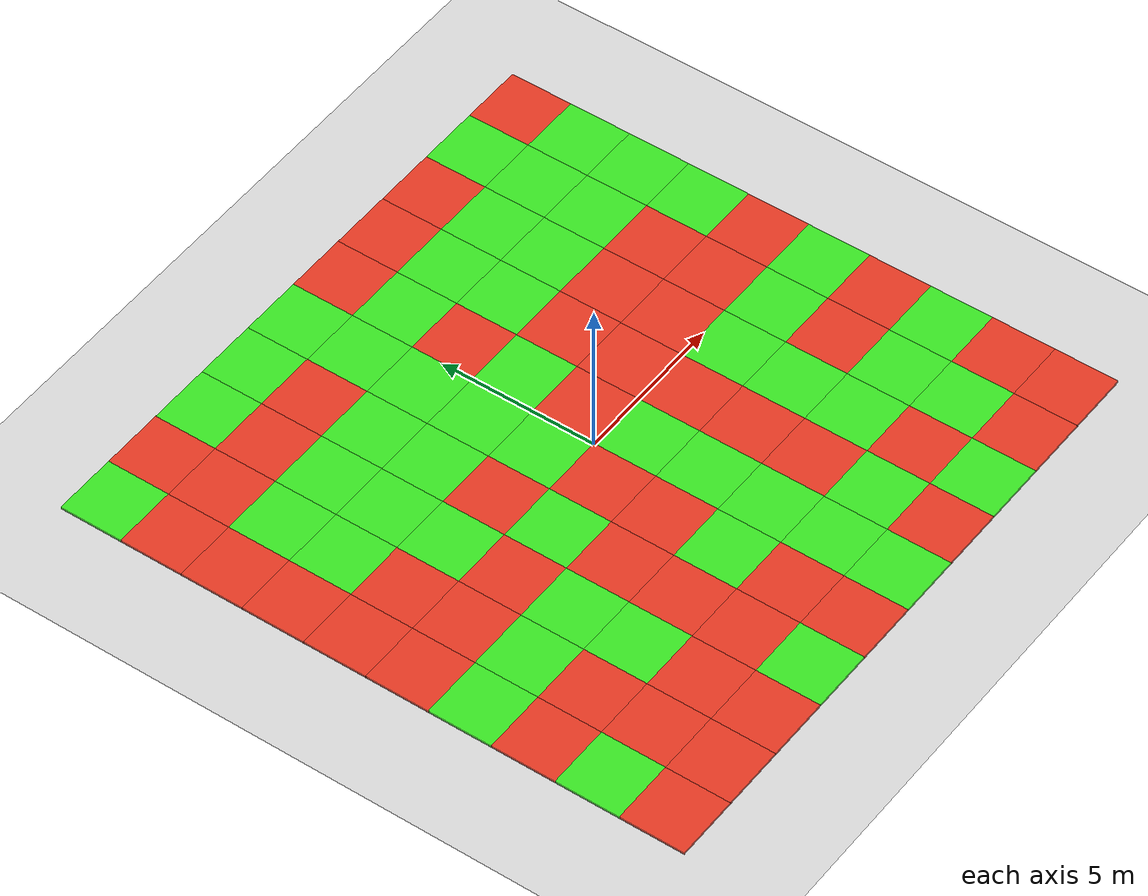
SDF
<?xml version="1.0" ?>
<sdf version='1.9'>
  <world name='car_world'>
    <physics name='1ms' type='ignored'>
      <max_step_size>0.001</max_step_size>
      <real_time_factor>1</real_time_factor>
      <real_time_update_rate>1000</real_time_update_rate>
    </physics>
    <plugin name='ignition::gazebo::systems::Physics' filename='libignition-gazebo-physics-system.so'/>
    <plugin name='ignition::gazebo::systems::UserCommands' filename='libignition-gazebo-user-commands-system.so'/>
    <plugin name='ignition::gazebo::systems::SceneBroadcaster' filename='libignition-gazebo-scene-broadcaster-system.so'/>
    <gravity>0 0 -9.8</gravity>
    <magnetic_field>6e-06 2.3e-05 -4.2e-05</magnetic_field>
    <atmosphere type='adiabatic'/>
    <scene>
      <ambient>0.4 0.4 0.4 1</ambient>
      <background>0.7 0.7 0.7 1</background>
      <shadows>true</shadows>
    </scene>
    <model name='ground_plane'>
      <static>true</static>
      <link name='link'>
        <collision name='collision'>
          <geometry>
            <plane>
              <normal>0 0 1</normal>
              <size>1 1</size>
            </plane>
          </geometry>
          <surface>
            <friction>
              <ode/>
            </friction>
            <bounce/>
            <contact/>
          </surface>
        </collision>
        <visual name='visual'>
          <geometry>
            <plane>
              <normal>0 0 1</normal>
              <size>100 100</size>
            </plane>
          </geometry>
          <material>
            <ambient>0.8 0.8 0.8 1</ambient>
            <diffuse>0.8 0.8 0.8 1</diffuse>
            <specular>0.8 0.8 0.8 1</specular>
          </material>
        </visual>
        <pose>0 0 0 0 -0 0</pose>
        <inertial>
          <pose>0 0 0 0 -0 0</pose>
          <mass>1</mass>
          <inertia>
            <ixx>1</ixx>
            <ixy>0</ixy>
            <ixz>0</ixz>
            <iyy>1</iyy>
            <iyz>0</iyz>
            <izz>1</izz>
          </inertia>
        </inertial>
        <enable_wind>false</enable_wind>
      </link>
      <pose>0 0 0 0 -0 0</pose>
      <self_collide>false</self_collide>
    </model>
    <model name='planks'>
      <pose>0 0 0 0 -0 0</pose>
      <include>
			  <uri>model://tiles/tile_00.sdf</uri>
		  </include>
      <include>
			  <uri>model://tiles/tile_01.sdf</uri>
		  </include>
      <include>
			  <uri>model://tiles/tile_02.sdf</uri>
		  </include>
      <include>
			  <uri>model://tiles/tile_03.sdf</uri>
		  </include>
      <include>
			  <uri>model://tiles/tile_04.sdf</uri>
		  </include>
      <include>
			  <uri>model://tiles/tile_05.sdf</uri>
		  </include>
      <include>
			  <uri>model://tiles/tile_06.sdf</uri>
		  </include>
      <include>
			  <uri>model://tiles/tile_07.sdf</uri>
		  </include>
      <include>
			  <uri>model://tiles/tile_08.sdf</uri>
		  </include>
      <include>
			  <uri>model://tiles/tile_09.sdf</uri>
		  </include>
      <include>
			  <uri>model://tiles/tile_10.sdf</uri>
		  </include>
      <include>
			  <uri>model://tiles/tile_11.sdf</uri>
		  </include>
      <include>
			  <uri>model://tiles/tile_12.sdf</uri>
		  </include>
      <include>
			  <uri>model://tiles/tile_13.sdf</uri>
		  </include>
      <include>
			  <uri>model://tiles/tile_14.sdf</uri>
		  </include>
      <include>
			  <uri>model://tiles/tile_15.sdf</uri>
		  </include>
      <include>
			  <uri>model://tiles/tile_16.sdf</uri>
		  </include>
      <include>
			  <uri>model://tiles/tile_17.sdf</uri>
		  </include>
      <include>
			  <uri>model://tiles/tile_18.sdf</uri>
		  </include>
      <include>
			  <uri>model://tiles/tile_19.sdf</uri>
      </include>
      <include>
			  <uri>model://tiles/tile_20.sdf</uri>
		  </include>
      <include>
			  <uri>model://tiles/tile_21.sdf</uri>
		  </include>
      <include>
			  <uri>model://tiles/tile_22.sdf</uri>
		  </include>
      <include>
			  <uri>model://tiles/tile_23.sdf</uri>
		  </include>
      <include>
			  <uri>model://tiles/tile_24.sdf</uri>
		  </include>
      <include>
			  <uri>model://tiles/tile_25.sdf</uri>
		  </include>
      <include>
			  <uri>model://tiles/tile_26.sdf</uri>
		  </include>
      <include>
			  <uri>model://tiles/tile_27.sdf</uri>
		  </include>
      <include>
			  <uri>model://tiles/tile_28.sdf</uri>
		  </include>
      <include>
			  <uri>model://tiles/tile_29.sdf</uri>
		  </include>
      <include>
			  <uri>model://tiles/tile_30.sdf</uri>
		  </include>
      <include>
			  <uri>model://tiles/tile_31.sdf</uri>
		  </include>
      <include>
			  <uri>model://tiles/tile_32.sdf</uri>
		  </include>
      <include>
			  <uri>model://tiles/tile_33.sdf</uri>
		  </include>
      <include>
			  <uri>model://tiles/tile_34.sdf</uri>
		  </include>
      <include>
			  <uri>model://tiles/tile_35.sdf</uri>
		  </include>
      <include>
			  <uri>model://tiles/tile_36.sdf</uri>
		  </include>
      <include>
			  <uri>model://tiles/tile_37.sdf</uri>
		  </include>
      <include>
			  <uri>model://tiles/tile_38.sdf</uri>
		  </include>
      <include>
			  <uri>model://tiles/tile_39.sdf</uri>
		  </include>
      <include>
			  <uri>model://tiles/tile_40.sdf</uri>
		  </include>
      <include>
			  <uri>model://tiles/tile_41.sdf</uri>
		  </include>
      <include>
			  <uri>model://tiles/tile_42.sdf</uri>
		  </include>
      <include>
			  <uri>model://tiles/tile_43.sdf</uri>
		  </include>
      <include>
			  <uri>model://tiles/tile_44.sdf</uri>
		  </include>
      <include>
			  <uri>model://tiles/tile_45.sdf</uri>
		  </include>
      <include>
			  <uri>model://tiles/tile_46.sdf</uri>
		  </include>
      <include>
			  <uri>model://tiles/tile_47.sdf</uri>
		  </include>
      <include>
			  <uri>model://tiles/tile_48.sdf</uri>
		  </include>
      <include>
			  <uri>model://tiles/tile_49.sdf</uri>
		  </include>
      <include>
			  <uri>model://tiles/tile_50.sdf</uri>
		  </include>
      <include>
			  <uri>model://tiles/tile_51.sdf</uri>
		  </include>
      <include>
			  <uri>model://tiles/tile_52.sdf</uri>
		  </include>
      <include>
			  <uri>model://tiles/tile_53.sdf</uri>
		  </include>
      <include>
			  <uri>model://tiles/tile_54.sdf</uri>
		  </include>
      <include>
			  <uri>model://tiles/tile_55.sdf</uri>
		  </include>
      <include>
			  <uri>model://tiles/tile_56.sdf</uri>
		  </include>
      <include>
			  <uri>model://tiles/tile_57.sdf</uri>
		  </include>
      <include>
			  <uri>model://tiles/tile_58.sdf</uri>
		  </include>
      <include>
			  <uri>model://tiles/tile_59.sdf</uri>
		  </include>
      <include>
			  <uri>model://tiles/tile_60.sdf</uri>
		  </include>
      <include>
			  <uri>model://tiles/tile_61.sdf</uri>
		  </include>
      <include>
			  <uri>model://tiles/tile_62.sdf</uri>
		  </include>
      <include>
			  <uri>model://tiles/tile_63.sdf</uri>
		  </include>
      <include>
			  <uri>model://tiles/tile_64.sdf</uri>
		  </include>
      <include>
			  <uri>model://tiles/tile_65.sdf</uri>
		  </include>
      <include>
			  <uri>model://tiles/tile_66.sdf</uri>
		  </include>
      <include>
			  <uri>model://tiles/tile_67.sdf</uri>
		  </include>
      <include>
			  <uri>model://tiles/tile_68.sdf</uri>
		  </include>
      <include>
			  <uri>model://tiles/tile_69.sdf</uri>
		  </include>
      <include>
			  <uri>model://tiles/tile_70.sdf</uri>
		  </include>
      <include>
			  <uri>model://tiles/tile_71.sdf</uri>
		  </include>
      <include>
			  <uri>model://tiles/tile_72.sdf</uri>
		  </include>
      <include>
			  <uri>model://tiles/tile_73.sdf</uri>
		  </include>
      <include>
			  <uri>model://tiles/tile_74.sdf</uri>
		  </include>
      <include>
			  <uri>model://tiles/tile_75.sdf</uri>
		  </include>
      <include>
			  <uri>model://tiles/tile_76.sdf</uri>
		  </include>
      <include>
			  <uri>model://tiles/tile_77.sdf</uri>
		  </include>
      <include>
			  <uri>model://tiles/tile_78.sdf</uri>
		  </include>
      <include>
			  <uri>model://tiles/tile_79.sdf</uri>
		  </include>
      <include>
			  <uri>model://tiles/tile_80.sdf</uri>
		  </include>
      <include>
			  <uri>model://tiles/tile_81.sdf</uri>
		  </include>
      <include>
			  <uri>model://tiles/tile_82.sdf</uri>
		  </include>
      <include>
			  <uri>model://tiles/tile_83.sdf</uri>
		  </include>
      <include>
			  <uri>model://tiles/tile_84.sdf</uri>
		  </include>
      <include>
			  <uri>model://tiles/tile_85.sdf</uri>
		  </include>
      <include>
			  <uri>model://tiles/tile_86.sdf</uri>
		  </include>
      <include>
			  <uri>model://tiles/tile_87.sdf</uri>
		  </include>
      <include>
			  <uri>model://tiles/tile_88.sdf</uri>
		  </include>
      <include>
			  <uri>model://tiles/tile_89.sdf</uri>
		  </include>
      <include>
			  <uri>model://tiles/tile_90.sdf</uri>
		  </include>
      <include>
			  <uri>model://tiles/tile_91.sdf</uri>
		  </include>
      <include>
			  <uri>model://tiles/tile_92.sdf</uri>
		  </include>
      <include>
			  <uri>model://tiles/tile_93.sdf</uri>
		  </include>
      <include>
			  <uri>model://tiles/tile_94.sdf</uri>
		  </include>
      <include>
			  <uri>model://tiles/tile_95.sdf</uri>
		  </include>
      <include>
			  <uri>model://tiles/tile_96.sdf</uri>
		  </include>
      <include>
			  <uri>model://tiles/tile_97.sdf</uri>
		  </include>
      <include>
			  <uri>model://tiles/tile_98.sdf</uri>
		  </include>
      <include>
			  <uri>model://tiles/tile_99.sdf</uri>
		  </include>
      <static>false</static>
      <self_collide>false</self_collide>
      <static>false</static>
      <self_collide>false</self_collide>

    </model>
    <light name='sun' type='directional'>
      <pose>0 0 10 0 -0 0</pose>
      <cast_shadows>true</cast_shadows>
      <intensity>1</intensity>
      <direction>-0.5 0.1 -0.9</direction>
      <diffuse>0.8 0.8 0.8 1</diffuse>
      <specular>0.2 0.2 0.2 1</specular>
      <attenuation>
        <range>1000</range>
        <linear>0.01</linear>
        <constant>0.90000000000000002</constant>
        <quadratic>0.001</quadratic>
      </attenuation>
      <spot>
        <inner_angle>0</inner_angle>
        <outer_angle>0</outer_angle>
        <falloff>0</falloff>
      </spot>
    </light>
  </world>
</sdf>

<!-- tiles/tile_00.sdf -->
<sdf version="1.6">
  <model name="tile_-5_-5">
    <pose>-9 -9 0 0 0 0</pose>
      <link name="tile_-5_-5">
        <pose>0 0 0 0 -0 0</pose>
        <inertial>
          <mass>260.134</mass>
          <inertia>
            <ixx>86.8209</ixx>
            <ixy>0</ixy>
            <ixz>0</ixz>
            <iyy>86.8213</iyy>
            <iyz>0</iyz>
            <izz>173.423</izz>
          </inertia>
          <pose>0 0 0 0 -0 0</pose>
        </inertial>
        <visual name='visual'>
          <geometry>
            <box>
              <size>2 2 0.1</size>
            </box>
          </geometry>
          <material>
            <ambient>0.9 0.1 0 0.8</ambient>
            <diffuse>0.9 0.1 0 0.8</diffuse>
            <specular>0.9 0.1 0 0.8</specular>
          </material>
        </visual>
        <collision name='collision'>
          <geometry>
            <box>
              <size>2 2 0.1</size>
            </box>
          </geometry>
          <surface>
            <friction>
              <ode>
                <mu>44.0</mu>
                <mu2>4.0</mu2>
              </ode>
            </friction>
            <bounce/>
            <contact/>
          </surface>
        </collision>
        <enable_wind>false</enable_wind>
      </link>
  </model>
</sdf>

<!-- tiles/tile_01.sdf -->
<sdf version="1.6">
  <model name="tile_-5_-4">
    <pose>-9 -7 0 0 0 0</pose>
      <link name="tile_-5_-4">
        <pose>0 0 0 0 -0 0</pose>
        <inertial>
          <mass>260.134</mass>
          <inertia>
            <ixx>86.8209</ixx>
            <ixy>0</ixy>
            <ixz>0</ixz>
            <iyy>86.8213</iyy>
            <iyz>0</iyz>
            <izz>173.423</izz>
          </inertia>
          <pose>0 0 0 0 -0 0</pose>
        </inertial>
        <visual name='visual'>
          <geometry>
            <box>
              <size>2 2 0.1</size>
            </box>
          </geometry>
          <material>
            <ambient>0.1 0.9 0 0.8</ambient>
            <diffuse>0.1 0.9 0 0.8</diffuse>
            <specular>0.1 0.9 0 0.8</specular>
          </material>
        </visual>
        <collision name='collision'>
          <geometry>
            <box>
              <size>2 2 0.1</size>
            </box>
          </geometry>
          <surface>
            <friction>
              <ode>
                <mu>86.0</mu>
                <mu2>5.0</mu2>
              </ode>
            </friction>
            <bounce/>
            <contact/>
          </surface>
        </collision>
        <enable_wind>false</enable_wind>
      </link>
  </model>
</sdf>

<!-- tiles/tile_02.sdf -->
<sdf version="1.6">
  <model name="tile_-5_-3">
    <pose>-9 -5 0 0 0 0</pose>
      <link name="tile_-5_-3">
        <pose>0 0 0 0 -0 0</pose>
        <inertial>
          <mass>260.134</mass>
          <inertia>
            <ixx>86.8209</ixx>
            <ixy>0</ixy>
            <ixz>0</ixz>
            <iyy>86.8213</iyy>
            <iyz>0</iyz>
            <izz>173.423</izz>
          </inertia>
          <pose>0 0 0 0 -0 0</pose>
        </inertial>
        <visual name='visual'>
          <geometry>
            <box>
              <size>2 2 0.1</size>
            </box>
          </geometry>
          <material>
            <ambient>0.9 0.1 0 0.8</ambient>
            <diffuse>0.9 0.1 0 0.8</diffuse>
            <specular>0.9 0.1 0 0.8</specular>
          </material>
        </visual>
        <collision name='collision'>
          <geometry>
            <box>
              <size>2 2 0.1</size>
            </box>
          </geometry>
          <surface>
            <friction>
              <ode>
                <mu>8.0</mu>
                <mu2>35.0</mu2>
              </ode>
            </friction>
            <bounce/>
            <contact/>
          </surface>
        </collision>
        <enable_wind>false</enable_wind>
      </link>
  </model>
</sdf>

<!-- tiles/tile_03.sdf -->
<sdf version="1.6">
  <model name="tile_-5_-2">
    <pose>-9 -3 0 0 0 0</pose>
      <link name="tile_-5_-2">
        <pose>0 0 0 0 -0 0</pose>
        <inertial>
          <mass>260.134</mass>
          <inertia>
            <ixx>86.8209</ixx>
            <ixy>0</ixy>
            <ixz>0</ixz>
            <iyy>86.8213</iyy>
            <iyz>0</iyz>
            <izz>173.423</izz>
          </inertia>
          <pose>0 0 0 0 -0 0</pose>
        </inertial>
        <visual name='visual'>
          <geometry>
            <box>
              <size>2 2 0.1</size>
            </box>
          </geometry>
          <material>
            <ambient>0.1 0.9 0 0.8</ambient>
            <diffuse>0.1 0.9 0 0.8</diffuse>
            <specular>0.1 0.9 0 0.8</specular>
          </material>
        </visual>
        <collision name='collision'>
          <geometry>
            <box>
              <size>2 2 0.1</size>
            </box>
          </geometry>
          <surface>
            <friction>
              <ode>
                <mu>55.00000000000001</mu>
                <mu2>54.0</mu2>
              </ode>
            </friction>
            <bounce/>
            <contact/>
          </surface>
        </collision>
        <enable_wind>false</enable_wind>
      </link>
  </model>
</sdf>

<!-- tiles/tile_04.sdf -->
<sdf version="1.6">
  <model name="tile_-5_-1">
    <pose>-9 -1 0 0 0 0</pose>
      <link name="tile_-5_-1">
        <pose>0 0 0 0 -0 0</pose>
        <inertial>
          <mass>260.134</mass>
          <inertia>
            <ixx>86.8209</ixx>
            <ixy>0</ixy>
            <ixz>0</ixz>
            <iyy>86.8213</iyy>
            <iyz>0</iyz>
            <izz>173.423</izz>
          </inertia>
          <pose>0 0 0 0 -0 0</pose>
        </inertial>
        <visual name='visual'>
          <geometry>
            <box>
              <size>2 2 0.1</size>
            </box>
          </geometry>
          <material>
            <ambient>0.9 0.1 0 0.8</ambient>
            <diffuse>0.9 0.1 0 0.8</diffuse>
            <specular>0.9 0.1 0 0.8</specular>
          </material>
        </visual>
        <collision name='collision'>
          <geometry>
            <box>
              <size>2 2 0.1</size>
            </box>
          </geometry>
          <surface>
            <friction>
              <ode>
                <mu>46.0</mu>
                <mu2>69.0</mu2>
              </ode>
            </friction>
            <bounce/>
            <contact/>
          </surface>
        </collision>
        <enable_wind>false</enable_wind>
      </link>
  </model>
</sdf>

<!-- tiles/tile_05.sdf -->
<sdf version="1.6">
  <model name="tile_-5_0">
    <pose>-9 1 0 0 0 0</pose>
      <link name="tile_-5_0">
        <pose>0 0 0 0 -0 0</pose>
        <inertial>
          <mass>260.134</mass>
          <inertia>
            <ixx>86.8209</ixx>
            <ixy>0</ixy>
            <ixz>0</ixz>
            <iyy>86.8213</iyy>
            <iyz>0</iyz>
            <izz>173.423</izz>
          </inertia>
          <pose>0 0 0 0 -0 0</pose>
        </inertial>
        <visual name='visual'>
          <geometry>
            <box>
              <size>2 2 0.1</size>
            </box>
          </geometry>
          <material>
            <ambient>0.9 0.1 0 0.8</ambient>
            <diffuse>0.9 0.1 0 0.8</diffuse>
            <specular>0.9 0.1 0 0.8</specular>
          </material>
        </visual>
        <collision name='collision'>
          <geometry>
            <box>
              <size>2 2 0.1</size>
            </box>
          </geometry>
          <surface>
            <friction>
              <ode>
                <mu>40.0</mu>
                <mu2>16.0</mu2>
              </ode>
            </friction>
            <bounce/>
            <contact/>
          </surface>
        </collision>
        <enable_wind>false</enable_wind>
      </link>
  </model>
</sdf>

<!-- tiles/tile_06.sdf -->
<sdf version="1.6">
  <model name="tile_-5_1">
    <pose>-9 3 0 0 0 0</pose>
      <link name="tile_-5_1">
        <pose>0 0 0 0 -0 0</pose>
        <inertial>
          <mass>260.134</mass>
          <inertia>
            <ixx>86.8209</ixx>
            <ixy>0</ixy>
            <ixz>0</ixz>
            <iyy>86.8213</iyy>
            <iyz>0</iyz>
            <izz>173.423</izz>
          </inertia>
          <pose>0 0 0 0 -0 0</pose>
        </inertial>
        <visual name='visual'>
          <geometry>
            <box>
              <size>2 2 0.1</size>
            </box>
          </geometry>
          <material>
            <ambient>0.9 0.1 0 0.8</ambient>
            <diffuse>0.9 0.1 0 0.8</diffuse>
            <specular>0.9 0.1 0 0.8</specular>
          </material>
        </visual>
        <collision name='collision'>
          <geometry>
            <box>
              <size>2 2 0.1</size>
            </box>
          </geometry>
          <surface>
            <friction>
              <ode>
                <mu>13.0</mu>
                <mu2>96.0</mu2>
              </ode>
            </friction>
            <bounce/>
            <contact/>
          </surface>
        </collision>
        <enable_wind>false</enable_wind>
      </link>
  </model>
</sdf>

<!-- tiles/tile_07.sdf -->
<sdf version="1.6">
  <model name="tile_-5_2">
    <pose>-9 5 0 0 0 0</pose>
      <link name="tile_-5_2">
        <pose>0 0 0 0 -0 0</pose>
        <inertial>
          <mass>260.134</mass>
          <inertia>
            <ixx>86.8209</ixx>
            <ixy>0</ixy>
            <ixz>0</ixz>
            <iyy>86.8213</iyy>
            <iyz>0</iyz>
            <izz>173.423</izz>
          </inertia>
          <pose>0 0 0 0 -0 0</pose>
        </inertial>
        <visual name='visual'>
          <geometry>
            <box>
              <size>2 2 0.1</size>
            </box>
          </geometry>
          <material>
            <ambient>0.9 0.1 0 0.8</ambient>
            <diffuse>0.9 0.1 0 0.8</diffuse>
            <specular>0.9 0.1 0 0.8</specular>
          </material>
        </visual>
        <collision name='collision'>
          <geometry>
            <box>
              <size>2 2 0.1</size>
            </box>
          </geometry>
          <surface>
            <friction>
              <ode>
                <mu>16.0</mu>
                <mu2>18.0</mu2>
              </ode>
            </friction>
            <bounce/>
            <contact/>
          </surface>
        </collision>
        <enable_wind>false</enable_wind>
      </link>
  </model>
</sdf>

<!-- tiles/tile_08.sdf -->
<sdf version="1.6">
  <model name="tile_-5_3">
    <pose>-9 7 0 0 0 0</pose>
      <link name="tile_-5_3">
        <pose>0 0 0 0 -0 0</pose>
        <inertial>
          <mass>260.134</mass>
          <inertia>
            <ixx>86.8209</ixx>
            <ixy>0</ixy>
            <ixz>0</ixz>
            <iyy>86.8213</iyy>
            <iyz>0</iyz>
            <izz>173.423</izz>
          </inertia>
          <pose>0 0 0 0 -0 0</pose>
        </inertial>
        <visual name='visual'>
          <geometry>
            <box>
              <size>2 2 0.1</size>
            </box>
          </geometry>
          <material>
            <ambient>0.9 0.1 0 0.8</ambient>
            <diffuse>0.9 0.1 0 0.8</diffuse>
            <specular>0.9 0.1 0 0.8</specular>
          </material>
        </visual>
        <collision name='collision'>
          <geometry>
            <box>
              <size>2 2 0.1</size>
            </box>
          </geometry>
          <surface>
            <friction>
              <ode>
                <mu>11.0</mu>
                <mu2>15.0</mu2>
              </ode>
            </friction>
            <bounce/>
            <contact/>
          </surface>
        </collision>
        <enable_wind>false</enable_wind>
      </link>
  </model>
</sdf>

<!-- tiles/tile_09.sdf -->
<sdf version="1.6">
  <model name="tile_-5_4">
    <pose>-9 9 0 0 0 0</pose>
      <link name="tile_-5_4">
        <pose>0 0 0 0 -0 0</pose>
        <inertial>
          <mass>260.134</mass>
          <inertia>
            <ixx>86.8209</ixx>
            <ixy>0</ixy>
            <ixz>0</ixz>
            <iyy>86.8213</iyy>
            <iyz>0</iyz>
            <izz>173.423</izz>
          </inertia>
          <pose>0 0 0 0 -0 0</pose>
        </inertial>
        <visual name='visual'>
          <geometry>
            <box>
              <size>2 2 0.1</size>
            </box>
          </geometry>
          <material>
            <ambient>0.1 0.9 0 0.8</ambient>
            <diffuse>0.1 0.9 0 0.8</diffuse>
            <specular>0.1 0.9 0 0.8</specular>
          </material>
        </visual>
        <collision name='collision'>
          <geometry>
            <box>
              <size>2 2 0.1</size>
            </box>
          </geometry>
          <surface>
            <friction>
              <ode>
                <mu>89.0</mu>
                <mu2>5.0</mu2>
              </ode>
            </friction>
            <bounce/>
            <contact/>
          </surface>
        </collision>
        <enable_wind>false</enable_wind>
      </link>
  </model>
</sdf>

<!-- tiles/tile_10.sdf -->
<sdf version="1.6">
  <model name="tile_-4_-5">
    <pose>-7 -9 0 0 0 0</pose>
      <link name="tile_-4_-5">
        <pose>0 0 0 0 -0 0</pose>
        <inertial>
          <mass>260.134</mass>
          <inertia>
            <ixx>86.8209</ixx>
            <ixy>0</ixy>
            <ixz>0</ixz>
            <iyy>86.8213</iyy>
            <iyz>0</iyz>
            <izz>173.423</izz>
          </inertia>
          <pose>0 0 0 0 -0 0</pose>
        </inertial>
        <visual name='visual'>
          <geometry>
            <box>
              <size>2 2 0.1</size>
            </box>
          </geometry>
          <material>
            <ambient>0.9 0.1 0 0.8</ambient>
            <diffuse>0.9 0.1 0 0.8</diffuse>
            <specular>0.9 0.1 0 0.8</specular>
          </material>
        </visual>
        <collision name='collision'>
          <geometry>
            <box>
              <size>2 2 0.1</size>
            </box>
          </geometry>
          <surface>
            <friction>
              <ode>
                <mu>14.000000000000002</mu>
                <mu2>87.0</mu2>
              </ode>
            </friction>
            <bounce/>
            <contact/>
          </surface>
        </collision>
        <enable_wind>false</enable_wind>
      </link>
  </model>
</sdf>

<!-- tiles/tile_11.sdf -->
<sdf version="1.6">
  <model name="tile_-4_-4">
    <pose>-7 -7 0 0 0 0</pose>
      <link name="tile_-4_-4">
        <pose>0 0 0 0 -0 0</pose>
        <inertial>
          <mass>260.134</mass>
          <inertia>
            <ixx>86.8209</ixx>
            <ixy>0</ixy>
            <ixz>0</ixz>
            <iyy>86.8213</iyy>
            <iyz>0</iyz>
            <izz>173.423</izz>
          </inertia>
          <pose>0 0 0 0 -0 0</pose>
        </inertial>
        <visual name='visual'>
          <geometry>
            <box>
              <size>2 2 0.1</size>
            </box>
          </geometry>
          <material>
            <ambient>0.9 0.1 0 0.8</ambient>
            <diffuse>0.9 0.1 0 0.8</diffuse>
            <specular>0.9 0.1 0 0.8</specular>
          </material>
        </visual>
        <collision name='collision'>
          <geometry>
            <box>
              <size>2 2 0.1</size>
            </box>
          </geometry>
          <surface>
            <friction>
              <ode>
                <mu>26.0</mu>
                <mu2>62.0</mu2>
              </ode>
            </friction>
            <bounce/>
            <contact/>
          </surface>
        </collision>
        <enable_wind>false</enable_wind>
      </link>
  </model>
</sdf>

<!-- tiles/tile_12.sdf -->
<sdf version="1.6">
  <model name="tile_-4_-3">
    <pose>-7 -5 0 0 0 0</pose>
      <link name="tile_-4_-3">
        <pose>0 0 0 0 -0 0</pose>
        <inertial>
          <mass>260.134</mass>
          <inertia>
            <ixx>86.8209</ixx>
            <ixy>0</ixy>
            <ixz>0</ixz>
            <iyy>86.8213</iyy>
            <iyz>0</iyz>
            <izz>173.423</izz>
          </inertia>
          <pose>0 0 0 0 -0 0</pose>
        </inertial>
        <visual name='visual'>
          <geometry>
            <box>
              <size>2 2 0.1</size>
            </box>
          </geometry>
          <material>
            <ambient>0.9 0.1 0 0.8</ambient>
            <diffuse>0.9 0.1 0 0.8</diffuse>
            <specular>0.9 0.1 0 0.8</specular>
          </material>
        </visual>
        <collision name='collision'>
          <geometry>
            <box>
              <size>2 2 0.1</size>
            </box>
          </geometry>
          <surface>
            <friction>
              <ode>
                <mu>45.0</mu>
                <mu2>14.000000000000002</mu2>
              </ode>
            </friction>
            <bounce/>
            <contact/>
          </surface>
        </collision>
        <enable_wind>false</enable_wind>
      </link>
  </model>
</sdf>

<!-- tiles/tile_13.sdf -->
<sdf version="1.6">
  <model name="tile_-4_-2">
    <pose>-7 -3 0 0 0 0</pose>
      <link name="tile_-4_-2">
        <pose>0 0 0 0 -0 0</pose>
        <inertial>
          <mass>260.134</mass>
          <inertia>
            <ixx>86.8209</ixx>
            <ixy>0</ixy>
            <ixz>0</ixz>
            <iyy>86.8213</iyy>
            <iyz>0</iyz>
            <izz>173.423</izz>
          </inertia>
          <pose>0 0 0 0 -0 0</pose>
        </inertial>
        <visual name='visual'>
          <geometry>
            <box>
              <size>2 2 0.1</size>
            </box>
          </geometry>
          <material>
            <ambient>0.1 0.9 0 0.8</ambient>
            <diffuse>0.1 0.9 0 0.8</diffuse>
            <specular>0.1 0.9 0 0.8</specular>
          </material>
        </visual>
        <collision name='collision'>
          <geometry>
            <box>
              <size>2 2 0.1</size>
            </box>
          </geometry>
          <surface>
            <friction>
              <ode>
                <mu>96.0</mu>
                <mu2>23.0</mu2>
              </ode>
            </friction>
            <bounce/>
            <contact/>
          </surface>
        </collision>
        <enable_wind>false</enable_wind>
      </link>
  </model>
</sdf>

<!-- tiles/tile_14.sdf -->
<sdf version="1.6">
  <model name="tile_-4_-1">
    <pose>-7 -1 0 0 0 0</pose>
      <link name="tile_-4_-1">
        <pose>0 0 0 0 -0 0</pose>
        <inertial>
          <mass>260.134</mass>
          <inertia>
            <ixx>86.8209</ixx>
            <ixy>0</ixy>
            <ixz>0</ixz>
            <iyy>86.8213</iyy>
            <iyz>0</iyz>
            <izz>173.423</izz>
          </inertia>
          <pose>0 0 0 0 -0 0</pose>
        </inertial>
        <visual name='visual'>
          <geometry>
            <box>
              <size>2 2 0.1</size>
            </box>
          </geometry>
          <material>
            <ambient>0.9 0.1 0 0.8</ambient>
            <diffuse>0.9 0.1 0 0.8</diffuse>
            <specular>0.9 0.1 0 0.8</specular>
          </material>
        </visual>
        <collision name='collision'>
          <geometry>
            <box>
              <size>2 2 0.1</size>
            </box>
          </geometry>
          <surface>
            <friction>
              <ode>
                <mu>25.0</mu>
                <mu2>98.0</mu2>
              </ode>
            </friction>
            <bounce/>
            <contact/>
          </surface>
        </collision>
        <enable_wind>false</enable_wind>
      </link>
  </model>
</sdf>

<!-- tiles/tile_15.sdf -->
<sdf version="1.6">
  <model name="tile_-4_0">
    <pose>-7 1 0 0 0 0</pose>
      <link name="tile_-4_0">
        <pose>0 0 0 0 -0 0</pose>
        <inertial>
          <mass>260.134</mass>
          <inertia>
            <ixx>86.8209</ixx>
            <ixy>0</ixy>
            <ixz>0</ixz>
            <iyy>86.8213</iyy>
            <iyz>0</iyz>
            <izz>173.423</izz>
          </inertia>
          <pose>0 0 0 0 -0 0</pose>
        </inertial>
        <visual name='visual'>
          <geometry>
            <box>
              <size>2 2 0.1</size>
            </box>
          </geometry>
          <material>
            <ambient>0.9 0.1 0 0.8</ambient>
            <diffuse>0.9 0.1 0 0.8</diffuse>
            <specular>0.9 0.1 0 0.8</specular>
          </material>
        </visual>
        <collision name='collision'>
          <geometry>
            <box>
              <size>2 2 0.1</size>
            </box>
          </geometry>
          <surface>
            <friction>
              <ode>
                <mu>24.0</mu>
                <mu2>20.0</mu2>
              </ode>
            </friction>
            <bounce/>
            <contact/>
          </surface>
        </collision>
        <enable_wind>false</enable_wind>
      </link>
  </model>
</sdf>

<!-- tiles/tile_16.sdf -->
<sdf version="1.6">
  <model name="tile_-4_1">
    <pose>-7 3 0 0 0 0</pose>
      <link name="tile_-4_1">
        <pose>0 0 0 0 -0 0</pose>
        <inertial>
          <mass>260.134</mass>
          <inertia>
            <ixx>86.8209</ixx>
            <ixy>0</ixy>
            <ixz>0</ixz>
            <iyy>86.8213</iyy>
            <iyz>0</iyz>
            <izz>173.423</izz>
          </inertia>
          <pose>0 0 0 0 -0 0</pose>
        </inertial>
        <visual name='visual'>
          <geometry>
            <box>
              <size>2 2 0.1</size>
            </box>
          </geometry>
          <material>
            <ambient>0.1 0.9 0 0.8</ambient>
            <diffuse>0.1 0.9 0 0.8</diffuse>
            <specular>0.1 0.9 0 0.8</specular>
          </material>
        </visual>
        <collision name='collision'>
          <geometry>
            <box>
              <size>2 2 0.1</size>
            </box>
          </geometry>
          <surface>
            <friction>
              <ode>
                <mu>56.99999999999999</mu>
                <mu2>7.000000000000001</mu2>
              </ode>
            </friction>
            <bounce/>
            <contact/>
          </surface>
        </collision>
        <enable_wind>false</enable_wind>
      </link>
  </model>
</sdf>

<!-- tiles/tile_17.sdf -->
<sdf version="1.6">
  <model name="tile_-4_2">
    <pose>-7 5 0 0 0 0</pose>
      <link name="tile_-4_2">
        <pose>0 0 0 0 -0 0</pose>
        <inertial>
          <mass>260.134</mass>
          <inertia>
            <ixx>86.8209</ixx>
            <ixy>0</ixy>
            <ixz>0</ixz>
            <iyy>86.8213</iyy>
            <iyz>0</iyz>
            <izz>173.423</izz>
          </inertia>
          <pose>0 0 0 0 -0 0</pose>
        </inertial>
        <visual name='visual'>
          <geometry>
            <box>
              <size>2 2 0.1</size>
            </box>
          </geometry>
          <material>
            <ambient>0.1 0.9 0 0.8</ambient>
            <diffuse>0.1 0.9 0 0.8</diffuse>
            <specular>0.1 0.9 0 0.8</specular>
          </material>
        </visual>
        <collision name='collision'>
          <geometry>
            <box>
              <size>2 2 0.1</size>
            </box>
          </geometry>
          <surface>
            <friction>
              <ode>
                <mu>51.0</mu>
                <mu2>97.0</mu2>
              </ode>
            </friction>
            <bounce/>
            <contact/>
          </surface>
        </collision>
        <enable_wind>false</enable_wind>
      </link>
  </model>
</sdf>

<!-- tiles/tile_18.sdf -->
<sdf version="1.6">
  <model name="tile_-4_3">
    <pose>-7 7 0 0 0 0</pose>
      <link name="tile_-4_3">
        <pose>0 0 0 0 -0 0</pose>
        <inertial>
          <mass>260.134</mass>
          <inertia>
            <ixx>86.8209</ixx>
            <ixy>0</ixy>
            <ixz>0</ixz>
            <iyy>86.8213</iyy>
            <iyz>0</iyz>
            <izz>173.423</izz>
          </inertia>
          <pose>0 0 0 0 -0 0</pose>
        </inertial>
        <visual name='visual'>
          <geometry>
            <box>
              <size>2 2 0.1</size>
            </box>
          </geometry>
          <material>
            <ambient>0.9 0.1 0 0.8</ambient>
            <diffuse>0.9 0.1 0 0.8</diffuse>
            <specular>0.9 0.1 0 0.8</specular>
          </material>
        </visual>
        <collision name='collision'>
          <geometry>
            <box>
              <size>2 2 0.1</size>
            </box>
          </geometry>
          <surface>
            <friction>
              <ode>
                <mu>41.0</mu>
                <mu2>26.0</mu2>
              </ode>
            </friction>
            <bounce/>
            <contact/>
          </surface>
        </collision>
        <enable_wind>false</enable_wind>
      </link>
  </model>
</sdf>

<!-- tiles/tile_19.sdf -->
<sdf version="1.6">
  <model name="tile_-4_4">
    <pose>-7 9 0 0 0 0</pose>
      <link name="tile_-4_4">
        <pose>0 0 0 0 -0 0</pose>
        <inertial>
          <mass>260.134</mass>
          <inertia>
            <ixx>86.8209</ixx>
            <ixy>0</ixy>
            <ixz>0</ixz>
            <iyy>86.8213</iyy>
            <iyz>0</iyz>
            <izz>173.423</izz>
          </inertia>
          <pose>0 0 0 0 -0 0</pose>
        </inertial>
        <visual name='visual'>
          <geometry>
            <box>
              <size>2 2 0.1</size>
            </box>
          </geometry>
          <material>
            <ambient>0.9 0.1 0 0.8</ambient>
            <diffuse>0.9 0.1 0 0.8</diffuse>
            <specular>0.9 0.1 0 0.8</specular>
          </material>
        </visual>
        <collision name='collision'>
          <geometry>
            <box>
              <size>2 2 0.1</size>
            </box>
          </geometry>
          <surface>
            <friction>
              <ode>
                <mu>47.0</mu>
                <mu2>85.0</mu2>
              </ode>
            </friction>
            <bounce/>
            <contact/>
          </surface>
        </collision>
        <enable_wind>false</enable_wind>
      </link>
  </model>
</sdf>

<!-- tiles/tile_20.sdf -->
<sdf version="1.6">
  <model name="tile_-3_-5">
    <pose>-5 -9 0 0 0 0</pose>
      <link name="tile_-3_-5">
        <pose>0 0 0 0 -0 0</pose>
        <inertial>
          <mass>260.134</mass>
          <inertia>
            <ixx>86.8209</ixx>
            <ixy>0</ixy>
            <ixz>0</ixz>
            <iyy>86.8213</iyy>
            <iyz>0</iyz>
            <izz>173.423</izz>
          </inertia>
          <pose>0 0 0 0 -0 0</pose>
        </inertial>
        <visual name='visual'>
          <geometry>
            <box>
              <size>2 2 0.1</size>
            </box>
          </geometry>
          <material>
            <ambient>0.9 0.1 0 0.8</ambient>
            <diffuse>0.9 0.1 0 0.8</diffuse>
            <specular>0.9 0.1 0 0.8</specular>
          </material>
        </visual>
        <collision name='collision'>
          <geometry>
            <box>
              <size>2 2 0.1</size>
            </box>
          </geometry>
          <surface>
            <friction>
              <ode>
                <mu>28.999999999999996</mu>
                <mu2>78.0</mu2>
              </ode>
            </friction>
            <bounce/>
            <contact/>
          </surface>
        </collision>
        <enable_wind>false</enable_wind>
      </link>
  </model>
</sdf>

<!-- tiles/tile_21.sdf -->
<sdf version="1.6">
  <model name="tile_-3_-4">
    <pose>-5 -7 0 0 0 0</pose>
      <link name="tile_-3_-4">
        <pose>0 0 0 0 -0 0</pose>
        <inertial>
          <mass>260.134</mass>
          <inertia>
            <ixx>86.8209</ixx>
            <ixy>0</ixy>
            <ixz>0</ixz>
            <iyy>86.8213</iyy>
            <iyz>0</iyz>
            <izz>173.423</izz>
          </inertia>
          <pose>0 0 0 0 -0 0</pose>
        </inertial>
        <visual name='visual'>
          <geometry>
            <box>
              <size>2 2 0.1</size>
            </box>
          </geometry>
          <material>
            <ambient>0.9 0.1 0 0.8</ambient>
            <diffuse>0.9 0.1 0 0.8</diffuse>
            <specular>0.9 0.1 0 0.8</specular>
          </material>
        </visual>
        <collision name='collision'>
          <geometry>
            <box>
              <size>2 2 0.1</size>
            </box>
          </geometry>
          <surface>
            <friction>
              <ode>
                <mu>42.0</mu>
                <mu2>49.0</mu2>
              </ode>
            </friction>
            <bounce/>
            <contact/>
          </surface>
        </collision>
        <enable_wind>false</enable_wind>
      </link>
  </model>
</sdf>

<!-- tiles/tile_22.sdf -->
<sdf version="1.6">
  <model name="tile_-3_-3">
    <pose>-5 -5 0 0 0 0</pose>
      <link name="tile_-3_-3">
        <pose>0 0 0 0 -0 0</pose>
        <inertial>
          <mass>260.134</mass>
          <inertia>
            <ixx>86.8209</ixx>
            <ixy>0</ixy>
            <ixz>0</ixz>
            <iyy>86.8213</iyy>
            <iyz>0</iyz>
            <izz>173.423</izz>
          </inertia>
          <pose>0 0 0 0 -0 0</pose>
        </inertial>
        <visual name='visual'>
          <geometry>
            <box>
              <size>2 2 0.1</size>
            </box>
          </geometry>
          <material>
            <ambient>0.1 0.9 0 0.8</ambient>
            <diffuse>0.1 0.9 0 0.8</diffuse>
            <specular>0.1 0.9 0 0.8</specular>
          </material>
        </visual>
        <collision name='collision'>
          <geometry>
            <box>
              <size>2 2 0.1</size>
            </box>
          </geometry>
          <surface>
            <friction>
              <ode>
                <mu>67.0</mu>
                <mu2>44.0</mu2>
              </ode>
            </friction>
            <bounce/>
            <contact/>
          </surface>
        </collision>
        <enable_wind>false</enable_wind>
      </link>
  </model>
</sdf>

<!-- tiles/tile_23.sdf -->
<sdf version="1.6">
  <model name="tile_-3_-2">
    <pose>-5 -3 0 0 0 0</pose>
      <link name="tile_-3_-2">
        <pose>0 0 0 0 -0 0</pose>
        <inertial>
          <mass>260.134</mass>
          <inertia>
            <ixx>86.8209</ixx>
            <ixy>0</ixy>
            <ixz>0</ixz>
            <iyy>86.8213</iyy>
            <iyz>0</iyz>
            <izz>173.423</izz>
          </inertia>
          <pose>0 0 0 0 -0 0</pose>
        </inertial>
        <visual name='visual'>
          <geometry>
            <box>
              <size>2 2 0.1</size>
            </box>
          </geometry>
          <material>
            <ambient>0.1 0.9 0 0.8</ambient>
            <diffuse>0.1 0.9 0 0.8</diffuse>
            <specular>0.1 0.9 0 0.8</specular>
          </material>
        </visual>
        <collision name='collision'>
          <geometry>
            <box>
              <size>2 2 0.1</size>
            </box>
          </geometry>
          <surface>
            <friction>
              <ode>
                <mu>94.0</mu>
                <mu2>20.0</mu2>
              </ode>
            </friction>
            <bounce/>
            <contact/>
          </surface>
        </collision>
        <enable_wind>false</enable_wind>
      </link>
  </model>
</sdf>

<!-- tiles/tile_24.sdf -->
<sdf version="1.6">
  <model name="tile_-3_-1">
    <pose>-5 -1 0 0 0 0</pose>
      <link name="tile_-3_-1">
        <pose>0 0 0 0 -0 0</pose>
        <inertial>
          <mass>260.134</mass>
          <inertia>
            <ixx>86.8209</ixx>
            <ixy>0</ixy>
            <ixz>0</ixz>
            <iyy>86.8213</iyy>
            <iyz>0</iyz>
            <izz>173.423</izz>
          </inertia>
          <pose>0 0 0 0 -0 0</pose>
        </inertial>
        <visual name='visual'>
          <geometry>
            <box>
              <size>2 2 0.1</size>
            </box>
          </geometry>
          <material>
            <ambient>0.9 0.1 0 0.8</ambient>
            <diffuse>0.9 0.1 0 0.8</diffuse>
            <specular>0.9 0.1 0 0.8</specular>
          </material>
        </visual>
        <collision name='collision'>
          <geometry>
            <box>
              <size>2 2 0.1</size>
            </box>
          </geometry>
          <surface>
            <friction>
              <ode>
                <mu>41.0</mu>
                <mu2>13.0</mu2>
              </ode>
            </friction>
            <bounce/>
            <contact/>
          </surface>
        </collision>
        <enable_wind>false</enable_wind>
      </link>
  </model>
</sdf>

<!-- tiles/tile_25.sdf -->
<sdf version="1.6">
  <model name="tile_-3_0">
    <pose>-5 1 0 0 0 0</pose>
      <link name="tile_-3_0">
        <pose>0 0 0 0 -0 0</pose>
        <inertial>
          <mass>260.134</mass>
          <inertia>
            <ixx>86.8209</ixx>
            <ixy>0</ixy>
            <ixz>0</ixz>
            <iyy>86.8213</iyy>
            <iyz>0</iyz>
            <izz>173.423</izz>
          </inertia>
          <pose>0 0 0 0 -0 0</pose>
        </inertial>
        <visual name='visual'>
          <geometry>
            <box>
              <size>2 2 0.1</size>
            </box>
          </geometry>
          <material>
            <ambient>0.1 0.9 0 0.8</ambient>
            <diffuse>0.1 0.9 0 0.8</diffuse>
            <specular>0.1 0.9 0 0.8</specular>
          </material>
        </visual>
        <collision name='collision'>
          <geometry>
            <box>
              <size>2 2 0.1</size>
            </box>
          </geometry>
          <surface>
            <friction>
              <ode>
                <mu>66.0</mu>
                <mu2>39.0</mu2>
              </ode>
            </friction>
            <bounce/>
            <contact/>
          </surface>
        </collision>
        <enable_wind>false</enable_wind>
      </link>
  </model>
</sdf>

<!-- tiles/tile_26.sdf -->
<sdf version="1.6">
  <model name="tile_-3_1">
    <pose>-5 3 0 0 0 0</pose>
      <link name="tile_-3_1">
        <pose>0 0 0 0 -0 0</pose>
        <inertial>
          <mass>260.134</mass>
          <inertia>
            <ixx>86.8209</ixx>
            <ixy>0</ixy>
            <ixz>0</ixz>
            <iyy>86.8213</iyy>
            <iyz>0</iyz>
            <izz>173.423</izz>
          </inertia>
          <pose>0 0 0 0 -0 0</pose>
        </inertial>
        <visual name='visual'>
          <geometry>
            <box>
              <size>2 2 0.1</size>
            </box>
          </geometry>
          <material>
            <ambient>0.1 0.9 0 0.8</ambient>
            <diffuse>0.1 0.9 0 0.8</diffuse>
            <specular>0.1 0.9 0 0.8</specular>
          </material>
        </visual>
        <collision name='collision'>
          <geometry>
            <box>
              <size>2 2 0.1</size>
            </box>
          </geometry>
          <surface>
            <friction>
              <ode>
                <mu>69.0</mu>
                <mu2>56.99999999999999</mu2>
              </ode>
            </friction>
            <bounce/>
            <contact/>
          </surface>
        </collision>
        <enable_wind>false</enable_wind>
      </link>
  </model>
</sdf>

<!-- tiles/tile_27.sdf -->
<sdf version="1.6">
  <model name="tile_-3_2">
    <pose>-5 5 0 0 0 0</pose>
      <link name="tile_-3_2">
        <pose>0 0 0 0 -0 0</pose>
        <inertial>
          <mass>260.134</mass>
          <inertia>
            <ixx>86.8209</ixx>
            <ixy>0</ixy>
            <ixz>0</ixz>
            <iyy>86.8213</iyy>
            <iyz>0</iyz>
            <izz>173.423</izz>
          </inertia>
          <pose>0 0 0 0 -0 0</pose>
        </inertial>
        <visual name='visual'>
          <geometry>
            <box>
              <size>2 2 0.1</size>
            </box>
          </geometry>
          <material>
            <ambient>0.1 0.9 0 0.8</ambient>
            <diffuse>0.1 0.9 0 0.8</diffuse>
            <specular>0.1 0.9 0 0.8</specular>
          </material>
        </visual>
        <collision name='collision'>
          <geometry>
            <box>
              <size>2 2 0.1</size>
            </box>
          </geometry>
          <surface>
            <friction>
              <ode>
                <mu>93.0</mu>
                <mu2>95.0</mu2>
              </ode>
            </friction>
            <bounce/>
            <contact/>
          </surface>
        </collision>
        <enable_wind>false</enable_wind>
      </link>
  </model>
</sdf>

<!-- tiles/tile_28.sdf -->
<sdf version="1.6">
  <model name="tile_-3_3">
    <pose>-5 7 0 0 0 0</pose>
      <link name="tile_-3_3">
        <pose>0 0 0 0 -0 0</pose>
        <inertial>
          <mass>260.134</mass>
          <inertia>
            <ixx>86.8209</ixx>
            <ixy>0</ixy>
            <ixz>0</ixz>
            <iyy>86.8213</iyy>
            <iyz>0</iyz>
            <izz>173.423</izz>
          </inertia>
          <pose>0 0 0 0 -0 0</pose>
        </inertial>
        <visual name='visual'>
          <geometry>
            <box>
              <size>2 2 0.1</size>
            </box>
          </geometry>
          <material>
            <ambient>0.9 0.1 0 0.8</ambient>
            <diffuse>0.9 0.1 0 0.8</diffuse>
            <specular>0.9 0.1 0 0.8</specular>
          </material>
        </visual>
        <collision name='collision'>
          <geometry>
            <box>
              <size>2 2 0.1</size>
            </box>
          </geometry>
          <surface>
            <friction>
              <ode>
                <mu>17.0</mu>
                <mu2>14.000000000000002</mu2>
              </ode>
            </friction>
            <bounce/>
            <contact/>
          </surface>
        </collision>
        <enable_wind>false</enable_wind>
      </link>
  </model>
</sdf>

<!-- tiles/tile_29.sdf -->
<sdf version="1.6">
  <model name="tile_-3_4">
    <pose>-5 9 0 0 0 0</pose>
      <link name="tile_-3_4">
        <pose>0 0 0 0 -0 0</pose>
        <inertial>
          <mass>260.134</mass>
          <inertia>
            <ixx>86.8209</ixx>
            <ixy>0</ixy>
            <ixz>0</ixz>
            <iyy>86.8213</iyy>
            <iyz>0</iyz>
            <izz>173.423</izz>
          </inertia>
          <pose>0 0 0 0 -0 0</pose>
        </inertial>
        <visual name='visual'>
          <geometry>
            <box>
              <size>2 2 0.1</size>
            </box>
          </geometry>
          <material>
            <ambient>0.1 0.9 0 0.8</ambient>
            <diffuse>0.1 0.9 0 0.8</diffuse>
            <specular>0.1 0.9 0 0.8</specular>
          </material>
        </visual>
        <collision name='collision'>
          <geometry>
            <box>
              <size>2 2 0.1</size>
            </box>
          </geometry>
          <surface>
            <friction>
              <ode>
                <mu>79.0</mu>
                <mu2>77.0</mu2>
              </ode>
            </friction>
            <bounce/>
            <contact/>
          </surface>
        </collision>
        <enable_wind>false</enable_wind>
      </link>
  </model>
</sdf>

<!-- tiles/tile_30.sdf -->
<sdf version="1.6">
  <model name="tile_-2_-5">
    <pose>-3 -9 0 0 0 0</pose>
      <link name="tile_-2_-5">
        <pose>0 0 0 0 -0 0</pose>
        <inertial>
          <mass>260.134</mass>
          <inertia>
            <ixx>86.8209</ixx>
            <ixy>0</ixy>
            <ixz>0</ixz>
            <iyy>86.8213</iyy>
            <iyz>0</iyz>
            <izz>173.423</izz>
          </inertia>
          <pose>0 0 0 0 -0 0</pose>
        </inertial>
        <visual name='visual'>
          <geometry>
            <box>
              <size>2 2 0.1</size>
            </box>
          </geometry>
          <material>
            <ambient>0.1 0.9 0 0.8</ambient>
            <diffuse>0.1 0.9 0 0.8</diffuse>
            <specular>0.1 0.9 0 0.8</specular>
          </material>
        </visual>
        <collision name='collision'>
          <geometry>
            <box>
              <size>2 2 0.1</size>
            </box>
          </geometry>
          <surface>
            <friction>
              <ode>
                <mu>86.0</mu>
                <mu2>13.0</mu2>
              </ode>
            </friction>
            <bounce/>
            <contact/>
          </surface>
        </collision>
        <enable_wind>false</enable_wind>
      </link>
  </model>
</sdf>

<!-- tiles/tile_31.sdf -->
<sdf version="1.6">
  <model name="tile_-2_-4">
    <pose>-3 -7 0 0 0 0</pose>
      <link name="tile_-2_-4">
        <pose>0 0 0 0 -0 0</pose>
        <inertial>
          <mass>260.134</mass>
          <inertia>
            <ixx>86.8209</ixx>
            <ixy>0</ixy>
            <ixz>0</ixz>
            <iyy>86.8213</iyy>
            <iyz>0</iyz>
            <izz>173.423</izz>
          </inertia>
          <pose>0 0 0 0 -0 0</pose>
        </inertial>
        <visual name='visual'>
          <geometry>
            <box>
              <size>2 2 0.1</size>
            </box>
          </geometry>
          <material>
            <ambient>0.9 0.1 0 0.8</ambient>
            <diffuse>0.9 0.1 0 0.8</diffuse>
            <specular>0.9 0.1 0 0.8</specular>
          </material>
        </visual>
        <collision name='collision'>
          <geometry>
            <box>
              <size>2 2 0.1</size>
            </box>
          </geometry>
          <surface>
            <friction>
              <ode>
                <mu>15.0</mu>
                <mu2>53.0</mu2>
              </ode>
            </friction>
            <bounce/>
            <contact/>
          </surface>
        </collision>
        <enable_wind>false</enable_wind>
      </link>
  </model>
</sdf>

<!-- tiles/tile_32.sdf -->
<sdf version="1.6">
  <model name="tile_-2_-3">
    <pose>-3 -5 0 0 0 0</pose>
      <link name="tile_-2_-3">
        <pose>0 0 0 0 -0 0</pose>
        <inertial>
          <mass>260.134</mass>
          <inertia>
            <ixx>86.8209</ixx>
            <ixy>0</ixy>
            <ixz>0</ixz>
            <iyy>86.8213</iyy>
            <iyz>0</iyz>
            <izz>173.423</izz>
          </inertia>
          <pose>0 0 0 0 -0 0</pose>
        </inertial>
        <visual name='visual'>
          <geometry>
            <box>
              <size>2 2 0.1</size>
            </box>
          </geometry>
          <material>
            <ambient>0.9 0.1 0 0.8</ambient>
            <diffuse>0.9 0.1 0 0.8</diffuse>
            <specular>0.9 0.1 0 0.8</specular>
          </material>
        </visual>
        <collision name='collision'>
          <geometry>
            <box>
              <size>2 2 0.1</size>
            </box>
          </geometry>
          <surface>
            <friction>
              <ode>
                <mu>31.0</mu>
                <mu2>89.0</mu2>
              </ode>
            </friction>
            <bounce/>
            <contact/>
          </surface>
        </collision>
        <enable_wind>false</enable_wind>
      </link>
  </model>
</sdf>

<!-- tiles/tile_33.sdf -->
<sdf version="1.6">
  <model name="tile_-2_-2">
    <pose>-3 -3 0 0 0 0</pose>
      <link name="tile_-2_-2">
        <pose>0 0 0 0 -0 0</pose>
        <inertial>
          <mass>260.134</mass>
          <inertia>
            <ixx>86.8209</ixx>
            <ixy>0</ixy>
            <ixz>0</ixz>
            <iyy>86.8213</iyy>
            <iyz>0</iyz>
            <izz>173.423</izz>
          </inertia>
          <pose>0 0 0 0 -0 0</pose>
        </inertial>
        <visual name='visual'>
          <geometry>
            <box>
              <size>2 2 0.1</size>
            </box>
          </geometry>
          <material>
            <ambient>0.9 0.1 0 0.8</ambient>
            <diffuse>0.9 0.1 0 0.8</diffuse>
            <specular>0.9 0.1 0 0.8</specular>
          </material>
        </visual>
        <collision name='collision'>
          <geometry>
            <box>
              <size>2 2 0.1</size>
            </box>
          </geometry>
          <surface>
            <friction>
              <ode>
                <mu>7.000000000000001</mu>
                <mu2>24.0</mu2>
              </ode>
            </friction>
            <bounce/>
            <contact/>
          </surface>
        </collision>
        <enable_wind>false</enable_wind>
      </link>
  </model>
</sdf>

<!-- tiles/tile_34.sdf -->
<sdf version="1.6">
  <model name="tile_-2_-1">
    <pose>-3 -1 0 0 0 0</pose>
      <link name="tile_-2_-1">
        <pose>0 0 0 0 -0 0</pose>
        <inertial>
          <mass>260.134</mass>
          <inertia>
            <ixx>86.8209</ixx>
            <ixy>0</ixy>
            <ixz>0</ixz>
            <iyy>86.8213</iyy>
            <iyz>0</iyz>
            <izz>173.423</izz>
          </inertia>
          <pose>0 0 0 0 -0 0</pose>
        </inertial>
        <visual name='visual'>
          <geometry>
            <box>
              <size>2 2 0.1</size>
            </box>
          </geometry>
          <material>
            <ambient>0.1 0.9 0 0.8</ambient>
            <diffuse>0.1 0.9 0 0.8</diffuse>
            <specular>0.1 0.9 0 0.8</specular>
          </material>
        </visual>
        <collision name='collision'>
          <geometry>
            <box>
              <size>2 2 0.1</size>
            </box>
          </geometry>
          <surface>
            <friction>
              <ode>
                <mu>61.0</mu>
                <mu2>20.0</mu2>
              </ode>
            </friction>
            <bounce/>
            <contact/>
          </surface>
        </collision>
        <enable_wind>false</enable_wind>
      </link>
  </model>
</sdf>

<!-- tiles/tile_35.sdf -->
<sdf version="1.6">
  <model name="tile_-2_0">
    <pose>-3 1 0 0 0 0</pose>
      <link name="tile_-2_0">
        <pose>0 0 0 0 -0 0</pose>
        <inertial>
          <mass>260.134</mass>
          <inertia>
            <ixx>86.8209</ixx>
            <ixy>0</ixy>
            <ixz>0</ixz>
            <iyy>86.8213</iyy>
            <iyz>0</iyz>
            <izz>173.423</izz>
          </inertia>
          <pose>0 0 0 0 -0 0</pose>
        </inertial>
        <visual name='visual'>
          <geometry>
            <box>
              <size>2 2 0.1</size>
            </box>
          </geometry>
          <material>
            <ambient>0.9 0.1 0 0.8</ambient>
            <diffuse>0.9 0.1 0 0.8</diffuse>
            <specular>0.9 0.1 0 0.8</specular>
          </material>
        </visual>
        <collision name='collision'>
          <geometry>
            <box>
              <size>2 2 0.1</size>
            </box>
          </geometry>
          <surface>
            <friction>
              <ode>
                <mu>8.0</mu>
                <mu2>75.0</mu2>
              </ode>
            </friction>
            <bounce/>
            <contact/>
          </surface>
        </collision>
        <enable_wind>false</enable_wind>
      </link>
  </model>
</sdf>

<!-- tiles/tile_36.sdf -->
<sdf version="1.6">
  <model name="tile_-2_1">
    <pose>-3 3 0 0 0 0</pose>
      <link name="tile_-2_1">
        <pose>0 0 0 0 -0 0</pose>
        <inertial>
          <mass>260.134</mass>
          <inertia>
            <ixx>86.8209</ixx>
            <ixy>0</ixy>
            <ixz>0</ixz>
            <iyy>86.8213</iyy>
            <iyz>0</iyz>
            <izz>173.423</izz>
          </inertia>
          <pose>0 0 0 0 -0 0</pose>
        </inertial>
        <visual name='visual'>
          <geometry>
            <box>
              <size>2 2 0.1</size>
            </box>
          </geometry>
          <material>
            <ambient>0.1 0.9 0 0.8</ambient>
            <diffuse>0.1 0.9 0 0.8</diffuse>
            <specular>0.1 0.9 0 0.8</specular>
          </material>
        </visual>
        <collision name='collision'>
          <geometry>
            <box>
              <size>2 2 0.1</size>
            </box>
          </geometry>
          <surface>
            <friction>
              <ode>
                <mu>65.0</mu>
                <mu2>48.0</mu2>
              </ode>
            </friction>
            <bounce/>
            <contact/>
          </surface>
        </collision>
        <enable_wind>false</enable_wind>
      </link>
  </model>
</sdf>

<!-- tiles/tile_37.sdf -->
<sdf version="1.6">
  <model name="tile_-2_2">
    <pose>-3 5 0 0 0 0</pose>
      <link name="tile_-2_2">
        <pose>0 0 0 0 -0 0</pose>
        <inertial>
          <mass>260.134</mass>
          <inertia>
            <ixx>86.8209</ixx>
            <ixy>0</ixy>
            <ixz>0</ixz>
            <iyy>86.8213</iyy>
            <iyz>0</iyz>
            <izz>173.423</izz>
          </inertia>
          <pose>0 0 0 0 -0 0</pose>
        </inertial>
        <visual name='visual'>
          <geometry>
            <box>
              <size>2 2 0.1</size>
            </box>
          </geometry>
          <material>
            <ambient>0.1 0.9 0 0.8</ambient>
            <diffuse>0.1 0.9 0 0.8</diffuse>
            <specular>0.1 0.9 0 0.8</specular>
          </material>
        </visual>
        <collision name='collision'>
          <geometry>
            <box>
              <size>2 2 0.1</size>
            </box>
          </geometry>
          <surface>
            <friction>
              <ode>
                <mu>62.0</mu>
                <mu2>88.0</mu2>
              </ode>
            </friction>
            <bounce/>
            <contact/>
          </surface>
        </collision>
        <enable_wind>false</enable_wind>
      </link>
  </model>
</sdf>

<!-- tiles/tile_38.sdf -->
<sdf version="1.6">
  <model name="tile_-2_3">
    <pose>-3 7 0 0 0 0</pose>
      <link name="tile_-2_3">
        <pose>0 0 0 0 -0 0</pose>
        <inertial>
          <mass>260.134</mass>
          <inertia>
            <ixx>86.8209</ixx>
            <ixy>0</ixy>
            <ixz>0</ixz>
            <iyy>86.8213</iyy>
            <iyz>0</iyz>
            <izz>173.423</izz>
          </inertia>
          <pose>0 0 0 0 -0 0</pose>
        </inertial>
        <visual name='visual'>
          <geometry>
            <box>
              <size>2 2 0.1</size>
            </box>
          </geometry>
          <material>
            <ambient>0.9 0.1 0 0.8</ambient>
            <diffuse>0.9 0.1 0 0.8</diffuse>
            <specular>0.9 0.1 0 0.8</specular>
          </material>
        </visual>
        <collision name='collision'>
          <geometry>
            <box>
              <size>2 2 0.1</size>
            </box>
          </geometry>
          <surface>
            <friction>
              <ode>
                <mu>24.0</mu>
                <mu2>59.0</mu2>
              </ode>
            </friction>
            <bounce/>
            <contact/>
          </surface>
        </collision>
        <enable_wind>false</enable_wind>
      </link>
  </model>
</sdf>

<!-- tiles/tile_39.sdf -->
<sdf version="1.6">
  <model name="tile_-2_4">
    <pose>-3 9 0 0 0 0</pose>
      <link name="tile_-2_4">
        <pose>0 0 0 0 -0 0</pose>
        <inertial>
          <mass>260.134</mass>
          <inertia>
            <ixx>86.8209</ixx>
            <ixy>0</ixy>
            <ixz>0</ixz>
            <iyy>86.8213</iyy>
            <iyz>0</iyz>
            <izz>173.423</izz>
          </inertia>
          <pose>0 0 0 0 -0 0</pose>
        </inertial>
        <visual name='visual'>
          <geometry>
            <box>
              <size>2 2 0.1</size>
            </box>
          </geometry>
          <material>
            <ambient>0.1 0.9 0 0.8</ambient>
            <diffuse>0.1 0.9 0 0.8</diffuse>
            <specular>0.1 0.9 0 0.8</specular>
          </material>
        </visual>
        <collision name='collision'>
          <geometry>
            <box>
              <size>2 2 0.1</size>
            </box>
          </geometry>
          <surface>
            <friction>
              <ode>
                <mu>73.0</mu>
                <mu2>32.0</mu2>
              </ode>
            </friction>
            <bounce/>
            <contact/>
          </surface>
        </collision>
        <enable_wind>false</enable_wind>
      </link>
  </model>
</sdf>

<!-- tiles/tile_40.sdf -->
<sdf version="1.6">
  <model name="tile_-1_-5">
    <pose>-1 -9 0 0 0 0</pose>
      <link name="tile_-1_-5">
        <pose>0 0 0 0 -0 0</pose>
        <inertial>
          <mass>260.134</mass>
          <inertia>
            <ixx>86.8209</ixx>
            <ixy>0</ixy>
            <ixz>0</ixz>
            <iyy>86.8213</iyy>
            <iyz>0</iyz>
            <izz>173.423</izz>
          </inertia>
          <pose>0 0 0 0 -0 0</pose>
        </inertial>
        <visual name='visual'>
          <geometry>
            <box>
              <size>2 2 0.1</size>
            </box>
          </geometry>
          <material>
            <ambient>0.9 0.1 0 0.8</ambient>
            <diffuse>0.9 0.1 0 0.8</diffuse>
            <specular>0.9 0.1 0 0.8</specular>
          </material>
        </visual>
        <collision name='collision'>
          <geometry>
            <box>
              <size>2 2 0.1</size>
            </box>
          </geometry>
          <surface>
            <friction>
              <ode>
                <mu>36.0</mu>
                <mu2>94.0</mu2>
              </ode>
            </friction>
            <bounce/>
            <contact/>
          </surface>
        </collision>
        <enable_wind>false</enable_wind>
      </link>
  </model>
</sdf>

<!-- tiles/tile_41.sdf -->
<sdf version="1.6">
  <model name="tile_-1_-4">
    <pose>-1 -7 0 0 0 0</pose>
      <link name="tile_-1_-4">
        <pose>0 0 0 0 -0 0</pose>
        <inertial>
          <mass>260.134</mass>
          <inertia>
            <ixx>86.8209</ixx>
            <ixy>0</ixy>
            <ixz>0</ixz>
            <iyy>86.8213</iyy>
            <iyz>0</iyz>
            <izz>173.423</izz>
          </inertia>
          <pose>0 0 0 0 -0 0</pose>
        </inertial>
        <visual name='visual'>
          <geometry>
            <box>
              <size>2 2 0.1</size>
            </box>
          </geometry>
          <material>
            <ambient>0.9 0.1 0 0.8</ambient>
            <diffuse>0.9 0.1 0 0.8</diffuse>
            <specular>0.9 0.1 0 0.8</specular>
          </material>
        </visual>
        <collision name='collision'>
          <geometry>
            <box>
              <size>2 2 0.1</size>
            </box>
          </geometry>
          <surface>
            <friction>
              <ode>
                <mu>25.0</mu>
                <mu2>54.0</mu2>
              </ode>
            </friction>
            <bounce/>
            <contact/>
          </surface>
        </collision>
        <enable_wind>false</enable_wind>
      </link>
  </model>
</sdf>

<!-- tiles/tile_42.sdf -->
<sdf version="1.6">
  <model name="tile_-1_-3">
    <pose>-1 -5 0 0 0 0</pose>
      <link name="tile_-1_-3">
        <pose>0 0 0 0 -0 0</pose>
        <inertial>
          <mass>260.134</mass>
          <inertia>
            <ixx>86.8209</ixx>
            <ixy>0</ixy>
            <ixz>0</ixz>
            <iyy>86.8213</iyy>
            <iyz>0</iyz>
            <izz>173.423</izz>
          </inertia>
          <pose>0 0 0 0 -0 0</pose>
        </inertial>
        <visual name='visual'>
          <geometry>
            <box>
              <size>2 2 0.1</size>
            </box>
          </geometry>
          <material>
            <ambient>0.1 0.9 0 0.8</ambient>
            <diffuse>0.1 0.9 0 0.8</diffuse>
            <specular>0.1 0.9 0 0.8</specular>
          </material>
        </visual>
        <collision name='collision'>
          <geometry>
            <box>
              <size>2 2 0.1</size>
            </box>
          </geometry>
          <surface>
            <friction>
              <ode>
                <mu>70.0</mu>
                <mu2>15.0</mu2>
              </ode>
            </friction>
            <bounce/>
            <contact/>
          </surface>
        </collision>
        <enable_wind>false</enable_wind>
      </link>
  </model>
</sdf>

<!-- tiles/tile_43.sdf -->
<sdf version="1.6">
  <model name="tile_-1_-2">
    <pose>-1 -3 0 0 0 0</pose>
      <link name="tile_-1_-2">
        <pose>0 0 0 0 -0 0</pose>
        <inertial>
          <mass>260.134</mass>
          <inertia>
            <ixx>86.8209</ixx>
            <ixy>0</ixy>
            <ixz>0</ixz>
            <iyy>86.8213</iyy>
            <iyz>0</iyz>
            <izz>173.423</izz>
          </inertia>
          <pose>0 0 0 0 -0 0</pose>
        </inertial>
        <visual name='visual'>
          <geometry>
            <box>
              <size>2 2 0.1</size>
            </box>
          </geometry>
          <material>
            <ambient>0.9 0.1 0 0.8</ambient>
            <diffuse>0.9 0.1 0 0.8</diffuse>
            <specular>0.9 0.1 0 0.8</specular>
          </material>
        </visual>
        <collision name='collision'>
          <geometry>
            <box>
              <size>2 2 0.1</size>
            </box>
          </geometry>
          <surface>
            <friction>
              <ode>
                <mu>3.0</mu>
                <mu2>56.00000000000001</mu2>
              </ode>
            </friction>
            <bounce/>
            <contact/>
          </surface>
        </collision>
        <enable_wind>false</enable_wind>
      </link>
  </model>
</sdf>

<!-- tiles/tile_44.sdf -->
<sdf version="1.6">
  <model name="tile_-1_-1">
    <pose>-1 -1 0 0 0 0</pose>
      <link name="tile_-1_-1">
        <pose>0 0 0 0 -0 0</pose>
        <inertial>
          <mass>260.134</mass>
          <inertia>
            <ixx>86.8209</ixx>
            <ixy>0</ixy>
            <ixz>0</ixz>
            <iyy>86.8213</iyy>
            <iyz>0</iyz>
            <izz>173.423</izz>
          </inertia>
          <pose>0 0 0 0 -0 0</pose>
        </inertial>
        <visual name='visual'>
          <geometry>
            <box>
              <size>2 2 0.1</size>
            </box>
          </geometry>
          <material>
            <ambient>0.9 0.1 0 0.8</ambient>
            <diffuse>0.9 0.1 0 0.8</diffuse>
            <specular>0.9 0.1 0 0.8</specular>
          </material>
        </visual>
        <collision name='collision'>
          <geometry>
            <box>
              <size>2 2 0.1</size>
            </box>
          </geometry>
          <surface>
            <friction>
              <ode>
                <mu>32.0</mu>
                <mu2>42.0</mu2>
              </ode>
            </friction>
            <bounce/>
            <contact/>
          </surface>
        </collision>
        <enable_wind>false</enable_wind>
      </link>
  </model>
</sdf>

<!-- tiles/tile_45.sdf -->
<sdf version="1.6">
  <model name="tile_-1_0">
    <pose>-1 1 0 0 0 0</pose>
      <link name="tile_-1_0">
        <pose>0 0 0 0 -0 0</pose>
        <inertial>
          <mass>260.134</mass>
          <inertia>
            <ixx>86.8209</ixx>
            <ixy>0</ixy>
            <ixz>0</ixz>
            <iyy>86.8213</iyy>
            <iyz>0</iyz>
            <izz>173.423</izz>
          </inertia>
          <pose>0 0 0 0 -0 0</pose>
        </inertial>
        <visual name='visual'>
          <geometry>
            <box>
              <size>2 2 0.1</size>
            </box>
          </geometry>
          <material>
            <ambient>0.1 0.9 0 0.8</ambient>
            <diffuse>0.1 0.9 0 0.8</diffuse>
            <specular>0.1 0.9 0 0.8</specular>
          </material>
        </visual>
        <collision name='collision'>
          <geometry>
            <box>
              <size>2 2 0.1</size>
            </box>
          </geometry>
          <surface>
            <friction>
              <ode>
                <mu>93.0</mu>
                <mu2>95.0</mu2>
              </ode>
            </friction>
            <bounce/>
            <contact/>
          </surface>
        </collision>
        <enable_wind>false</enable_wind>
      </link>
  </model>
</sdf>

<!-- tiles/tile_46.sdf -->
<sdf version="1.6">
  <model name="tile_-1_1">
    <pose>-1 3 0 0 0 0</pose>
      <link name="tile_-1_1">
        <pose>0 0 0 0 -0 0</pose>
        <inertial>
          <mass>260.134</mass>
          <inertia>
            <ixx>86.8209</ixx>
            <ixy>0</ixy>
            <ixz>0</ixz>
            <iyy>86.8213</iyy>
            <iyz>0</iyz>
            <izz>173.423</izz>
          </inertia>
          <pose>0 0 0 0 -0 0</pose>
        </inertial>
        <visual name='visual'>
          <geometry>
            <box>
              <size>2 2 0.1</size>
            </box>
          </geometry>
          <material>
            <ambient>0.1 0.9 0 0.8</ambient>
            <diffuse>0.1 0.9 0 0.8</diffuse>
            <specular>0.1 0.9 0 0.8</specular>
          </material>
        </visual>
        <collision name='collision'>
          <geometry>
            <box>
              <size>2 2 0.1</size>
            </box>
          </geometry>
          <surface>
            <friction>
              <ode>
                <mu>94.0</mu>
                <mu2>61.0</mu2>
              </ode>
            </friction>
            <bounce/>
            <contact/>
          </surface>
        </collision>
        <enable_wind>false</enable_wind>
      </link>
  </model>
</sdf>

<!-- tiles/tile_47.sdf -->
<sdf version="1.6">
  <model name="tile_-1_2">
    <pose>-1 5 0 0 0 0</pose>
      <link name="tile_-1_2">
        <pose>0 0 0 0 -0 0</pose>
        <inertial>
          <mass>260.134</mass>
          <inertia>
            <ixx>86.8209</ixx>
            <ixy>0</ixy>
            <ixz>0</ixz>
            <iyy>86.8213</iyy>
            <iyz>0</iyz>
            <izz>173.423</izz>
          </inertia>
          <pose>0 0 0 0 -0 0</pose>
        </inertial>
        <visual name='visual'>
          <geometry>
            <box>
              <size>2 2 0.1</size>
            </box>
          </geometry>
          <material>
            <ambient>0.1 0.9 0 0.8</ambient>
            <diffuse>0.1 0.9 0 0.8</diffuse>
            <specular>0.1 0.9 0 0.8</specular>
          </material>
        </visual>
        <collision name='collision'>
          <geometry>
            <box>
              <size>2 2 0.1</size>
            </box>
          </geometry>
          <surface>
            <friction>
              <ode>
                <mu>51.0</mu>
                <mu2>6.0</mu2>
              </ode>
            </friction>
            <bounce/>
            <contact/>
          </surface>
        </collision>
        <enable_wind>false</enable_wind>
      </link>
  </model>
</sdf>

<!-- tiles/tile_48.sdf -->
<sdf version="1.6">
  <model name="tile_-1_3">
    <pose>-1 7 0 0 0 0</pose>
      <link name="tile_-1_3">
        <pose>0 0 0 0 -0 0</pose>
        <inertial>
          <mass>260.134</mass>
          <inertia>
            <ixx>86.8209</ixx>
            <ixy>0</ixy>
            <ixz>0</ixz>
            <iyy>86.8213</iyy>
            <iyz>0</iyz>
            <izz>173.423</izz>
          </inertia>
          <pose>0 0 0 0 -0 0</pose>
        </inertial>
        <visual name='visual'>
          <geometry>
            <box>
              <size>2 2 0.1</size>
            </box>
          </geometry>
          <material>
            <ambient>0.1 0.9 0 0.8</ambient>
            <diffuse>0.1 0.9 0 0.8</diffuse>
            <specular>0.1 0.9 0 0.8</specular>
          </material>
        </visual>
        <collision name='collision'>
          <geometry>
            <box>
              <size>2 2 0.1</size>
            </box>
          </geometry>
          <surface>
            <friction>
              <ode>
                <mu>80.0</mu>
                <mu2>86.0</mu2>
              </ode>
            </friction>
            <bounce/>
            <contact/>
          </surface>
        </collision>
        <enable_wind>false</enable_wind>
      </link>
  </model>
</sdf>

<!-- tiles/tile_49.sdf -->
<sdf version="1.6">
  <model name="tile_-1_4">
    <pose>-1 9 0 0 0 0</pose>
      <link name="tile_-1_4">
        <pose>0 0 0 0 -0 0</pose>
        <inertial>
          <mass>260.134</mass>
          <inertia>
            <ixx>86.8209</ixx>
            <ixy>0</ixy>
            <ixz>0</ixz>
            <iyy>86.8213</iyy>
            <iyz>0</iyz>
            <izz>173.423</izz>
          </inertia>
          <pose>0 0 0 0 -0 0</pose>
        </inertial>
        <visual name='visual'>
          <geometry>
            <box>
              <size>2 2 0.1</size>
            </box>
          </geometry>
          <material>
            <ambient>0.1 0.9 0 0.8</ambient>
            <diffuse>0.1 0.9 0 0.8</diffuse>
            <specular>0.1 0.9 0 0.8</specular>
          </material>
        </visual>
        <collision name='collision'>
          <geometry>
            <box>
              <size>2 2 0.1</size>
            </box>
          </geometry>
          <surface>
            <friction>
              <ode>
                <mu>82.0</mu>
                <mu2>67.0</mu2>
              </ode>
            </friction>
            <bounce/>
            <contact/>
          </surface>
        </collision>
        <enable_wind>false</enable_wind>
      </link>
  </model>
</sdf>

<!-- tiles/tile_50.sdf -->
<sdf version="1.6">
  <model name="tile_0_-5">
    <pose>1 -9 0 0 0 0</pose>
      <link name="tile_0_-5">
        <pose>0 0 0 0 -0 0</pose>
        <inertial>
          <mass>260.134</mass>
          <inertia>
            <ixx>86.8209</ixx>
            <ixy>0</ixy>
            <ixz>0</ixz>
            <iyy>86.8213</iyy>
            <iyz>0</iyz>
            <izz>173.423</izz>
          </inertia>
          <pose>0 0 0 0 -0 0</pose>
        </inertial>
        <visual name='visual'>
          <geometry>
            <box>
              <size>2 2 0.1</size>
            </box>
          </geometry>
          <material>
            <ambient>0.1 0.9 0 0.8</ambient>
            <diffuse>0.1 0.9 0 0.8</diffuse>
            <specular>0.1 0.9 0 0.8</specular>
          </material>
        </visual>
        <collision name='collision'>
          <geometry>
            <box>
              <size>2 2 0.1</size>
            </box>
          </geometry>
          <surface>
            <friction>
              <ode>
                <mu>78.0</mu>
                <mu2>78.0</mu2>
              </ode>
            </friction>
            <bounce/>
            <contact/>
          </surface>
        </collision>
        <enable_wind>false</enable_wind>
      </link>
  </model>
</sdf>

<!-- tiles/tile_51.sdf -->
<sdf version="1.6">
  <model name="tile_0_-4">
    <pose>1 -7 0 0 0 0</pose>
      <link name="tile_0_-4">
        <pose>0 0 0 0 -0 0</pose>
        <inertial>
          <mass>260.134</mass>
          <inertia>
            <ixx>86.8209</ixx>
            <ixy>0</ixy>
            <ixz>0</ixz>
            <iyy>86.8213</iyy>
            <iyz>0</iyz>
            <izz>173.423</izz>
          </inertia>
          <pose>0 0 0 0 -0 0</pose>
        </inertial>
        <visual name='visual'>
          <geometry>
            <box>
              <size>2 2 0.1</size>
            </box>
          </geometry>
          <material>
            <ambient>0.1 0.9 0 0.8</ambient>
            <diffuse>0.1 0.9 0 0.8</diffuse>
            <specular>0.1 0.9 0 0.8</specular>
          </material>
        </visual>
        <collision name='collision'>
          <geometry>
            <box>
              <size>2 2 0.1</size>
            </box>
          </geometry>
          <surface>
            <friction>
              <ode>
                <mu>61.0</mu>
                <mu2>7.000000000000001</mu2>
              </ode>
            </friction>
            <bounce/>
            <contact/>
          </surface>
        </collision>
        <enable_wind>false</enable_wind>
      </link>
  </model>
</sdf>

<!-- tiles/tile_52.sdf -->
<sdf version="1.6">
  <model name="tile_0_-3">
    <pose>1 -5 0 0 0 0</pose>
      <link name="tile_0_-3">
        <pose>0 0 0 0 -0 0</pose>
        <inertial>
          <mass>260.134</mass>
          <inertia>
            <ixx>86.8209</ixx>
            <ixy>0</ixy>
            <ixz>0</ixz>
            <iyy>86.8213</iyy>
            <iyz>0</iyz>
            <izz>173.423</izz>
          </inertia>
          <pose>0 0 0 0 -0 0</pose>
        </inertial>
        <visual name='visual'>
          <geometry>
            <box>
              <size>2 2 0.1</size>
            </box>
          </geometry>
          <material>
            <ambient>0.1 0.9 0 0.8</ambient>
            <diffuse>0.1 0.9 0 0.8</diffuse>
            <specular>0.1 0.9 0 0.8</specular>
          </material>
        </visual>
        <collision name='collision'>
          <geometry>
            <box>
              <size>2 2 0.1</size>
            </box>
          </geometry>
          <surface>
            <friction>
              <ode>
                <mu>78.0</mu>
                <mu2>75.0</mu2>
              </ode>
            </friction>
            <bounce/>
            <contact/>
          </surface>
        </collision>
        <enable_wind>false</enable_wind>
      </link>
  </model>
</sdf>

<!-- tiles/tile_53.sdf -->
<sdf version="1.6">
  <model name="tile_0_-2">
    <pose>1 -3 0 0 0 0</pose>
      <link name="tile_0_-2">
        <pose>0 0 0 0 -0 0</pose>
        <inertial>
          <mass>260.134</mass>
          <inertia>
            <ixx>86.8209</ixx>
            <ixy>0</ixy>
            <ixz>0</ixz>
            <iyy>86.8213</iyy>
            <iyz>0</iyz>
            <izz>173.423</izz>
          </inertia>
          <pose>0 0 0 0 -0 0</pose>
        </inertial>
        <visual name='visual'>
          <geometry>
            <box>
              <size>2 2 0.1</size>
            </box>
          </geometry>
          <material>
            <ambient>0.1 0.9 0 0.8</ambient>
            <diffuse>0.1 0.9 0 0.8</diffuse>
            <specular>0.1 0.9 0 0.8</specular>
          </material>
        </visual>
        <collision name='collision'>
          <geometry>
            <box>
              <size>2 2 0.1</size>
            </box>
          </geometry>
          <surface>
            <friction>
              <ode>
                <mu>95.0</mu>
                <mu2>30.0</mu2>
              </ode>
            </friction>
            <bounce/>
            <contact/>
          </surface>
        </collision>
        <enable_wind>false</enable_wind>
      </link>
  </model>
</sdf>

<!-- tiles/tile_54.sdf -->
<sdf version="1.6">
  <model name="tile_0_-1">
    <pose>1 -1 0 0 0 0</pose>
      <link name="tile_0_-1">
        <pose>0 0 0 0 -0 0</pose>
        <inertial>
          <mass>260.134</mass>
          <inertia>
            <ixx>86.8209</ixx>
            <ixy>0</ixy>
            <ixz>0</ixz>
            <iyy>86.8213</iyy>
            <iyz>0</iyz>
            <izz>173.423</izz>
          </inertia>
          <pose>0 0 0 0 -0 0</pose>
        </inertial>
        <visual name='visual'>
          <geometry>
            <box>
              <size>2 2 0.1</size>
            </box>
          </geometry>
          <material>
            <ambient>0.1 0.9 0 0.8</ambient>
            <diffuse>0.1 0.9 0 0.8</diffuse>
            <specular>0.1 0.9 0 0.8</specular>
          </material>
        </visual>
        <collision name='collision'>
          <geometry>
            <box>
              <size>2 2 0.1</size>
            </box>
          </geometry>
          <surface>
            <friction>
              <ode>
                <mu>57.99999999999999</mu>
                <mu2>39.0</mu2>
              </ode>
            </friction>
            <bounce/>
            <contact/>
          </surface>
        </collision>
        <enable_wind>false</enable_wind>
      </link>
  </model>
</sdf>

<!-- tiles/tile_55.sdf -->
<sdf version="1.6">
  <model name="tile_0_0">
    <pose>1 1 0 0 0 0</pose>
      <link name="tile_0_0">
        <pose>0 0 0 0 -0 0</pose>
        <inertial>
          <mass>260.134</mass>
          <inertia>
            <ixx>86.8209</ixx>
            <ixy>0</ixy>
            <ixz>0</ixz>
            <iyy>86.8213</iyy>
            <iyz>0</iyz>
            <izz>173.423</izz>
          </inertia>
          <pose>0 0 0 0 -0 0</pose>
        </inertial>
        <visual name='visual'>
          <geometry>
            <box>
              <size>2 2 0.1</size>
            </box>
          </geometry>
          <material>
            <ambient>0.9 0.1 0 0.8</ambient>
            <diffuse>0.9 0.1 0 0.8</diffuse>
            <specular>0.9 0.1 0 0.8</specular>
          </material>
        </visual>
        <collision name='collision'>
          <geometry>
            <box>
              <size>2 2 0.1</size>
            </box>
          </geometry>
          <surface>
            <friction>
              <ode>
                <mu>22.0</mu>
                <mu2>66.0</mu2>
              </ode>
            </friction>
            <bounce/>
            <contact/>
          </surface>
        </collision>
        <enable_wind>false</enable_wind>
      </link>
  </model>
</sdf>

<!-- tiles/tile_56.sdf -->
<sdf version="1.6">
  <model name="tile_0_1">
    <pose>1 3 0 0 0 0</pose>
      <link name="tile_0_1">
        <pose>0 0 0 0 -0 0</pose>
        <inertial>
          <mass>260.134</mass>
          <inertia>
            <ixx>86.8209</ixx>
            <ixy>0</ixy>
            <ixz>0</ixz>
            <iyy>86.8213</iyy>
            <iyz>0</iyz>
            <izz>173.423</izz>
          </inertia>
          <pose>0 0 0 0 -0 0</pose>
        </inertial>
        <visual name='visual'>
          <geometry>
            <box>
              <size>2 2 0.1</size>
            </box>
          </geometry>
          <material>
            <ambient>0.1 0.9 0 0.8</ambient>
            <diffuse>0.1 0.9 0 0.8</diffuse>
            <specular>0.1 0.9 0 0.8</specular>
          </material>
        </visual>
        <collision name='collision'>
          <geometry>
            <box>
              <size>2 2 0.1</size>
            </box>
          </geometry>
          <surface>
            <friction>
              <ode>
                <mu>73.0</mu>
                <mu2>43.0</mu2>
              </ode>
            </friction>
            <bounce/>
            <contact/>
          </surface>
        </collision>
        <enable_wind>false</enable_wind>
      </link>
  </model>
</sdf>

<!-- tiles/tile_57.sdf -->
<sdf version="1.6">
  <model name="tile_0_2">
    <pose>1 5 0 0 0 0</pose>
      <link name="tile_0_2">
        <pose>0 0 0 0 -0 0</pose>
        <inertial>
          <mass>260.134</mass>
          <inertia>
            <ixx>86.8209</ixx>
            <ixy>0</ixy>
            <ixz>0</ixz>
            <iyy>86.8213</iyy>
            <iyz>0</iyz>
            <izz>173.423</izz>
          </inertia>
          <pose>0 0 0 0 -0 0</pose>
        </inertial>
        <visual name='visual'>
          <geometry>
            <box>
              <size>2 2 0.1</size>
            </box>
          </geometry>
          <material>
            <ambient>0.9 0.1 0 0.8</ambient>
            <diffuse>0.9 0.1 0 0.8</diffuse>
            <specular>0.9 0.1 0 0.8</specular>
          </material>
        </visual>
        <collision name='collision'>
          <geometry>
            <box>
              <size>2 2 0.1</size>
            </box>
          </geometry>
          <surface>
            <friction>
              <ode>
                <mu>36.0</mu>
                <mu2>53.0</mu2>
              </ode>
            </friction>
            <bounce/>
            <contact/>
          </surface>
        </collision>
        <enable_wind>false</enable_wind>
      </link>
  </model>
</sdf>

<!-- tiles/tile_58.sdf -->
<sdf version="1.6">
  <model name="tile_0_3">
    <pose>1 7 0 0 0 0</pose>
      <link name="tile_0_3">
        <pose>0 0 0 0 -0 0</pose>
        <inertial>
          <mass>260.134</mass>
          <inertia>
            <ixx>86.8209</ixx>
            <ixy>0</ixy>
            <ixz>0</ixz>
            <iyy>86.8213</iyy>
            <iyz>0</iyz>
            <izz>173.423</izz>
          </inertia>
          <pose>0 0 0 0 -0 0</pose>
        </inertial>
        <visual name='visual'>
          <geometry>
            <box>
              <size>2 2 0.1</size>
            </box>
          </geometry>
          <material>
            <ambient>0.1 0.9 0 0.8</ambient>
            <diffuse>0.1 0.9 0 0.8</diffuse>
            <specular>0.1 0.9 0 0.8</specular>
          </material>
        </visual>
        <collision name='collision'>
          <geometry>
            <box>
              <size>2 2 0.1</size>
            </box>
          </geometry>
          <surface>
            <friction>
              <ode>
                <mu>74.0</mu>
                <mu2>64.0</mu2>
              </ode>
            </friction>
            <bounce/>
            <contact/>
          </surface>
        </collision>
        <enable_wind>false</enable_wind>
      </link>
  </model>
</sdf>

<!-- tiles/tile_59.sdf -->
<sdf version="1.6">
  <model name="tile_0_4">
    <pose>1 9 0 0 0 0</pose>
      <link name="tile_0_4">
        <pose>0 0 0 0 -0 0</pose>
        <inertial>
          <mass>260.134</mass>
          <inertia>
            <ixx>86.8209</ixx>
            <ixy>0</ixy>
            <ixz>0</ixz>
            <iyy>86.8213</iyy>
            <iyz>0</iyz>
            <izz>173.423</izz>
          </inertia>
          <pose>0 0 0 0 -0 0</pose>
        </inertial>
        <visual name='visual'>
          <geometry>
            <box>
              <size>2 2 0.1</size>
            </box>
          </geometry>
          <material>
            <ambient>0.9 0.1 0 0.8</ambient>
            <diffuse>0.9 0.1 0 0.8</diffuse>
            <specular>0.9 0.1 0 0.8</specular>
          </material>
        </visual>
        <collision name='collision'>
          <geometry>
            <box>
              <size>2 2 0.1</size>
            </box>
          </geometry>
          <surface>
            <friction>
              <ode>
                <mu>32.0</mu>
                <mu2>3.0</mu2>
              </ode>
            </friction>
            <bounce/>
            <contact/>
          </surface>
        </collision>
        <enable_wind>false</enable_wind>
      </link>
  </model>
</sdf>

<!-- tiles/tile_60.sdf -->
<sdf version="1.6">
  <model name="tile_1_-5">
    <pose>3 -9 0 0 0 0</pose>
      <link name="tile_1_-5">
        <pose>0 0 0 0 -0 0</pose>
        <inertial>
          <mass>260.134</mass>
          <inertia>
            <ixx>86.8209</ixx>
            <ixy>0</ixy>
            <ixz>0</ixz>
            <iyy>86.8213</iyy>
            <iyz>0</iyz>
            <izz>173.423</izz>
          </inertia>
          <pose>0 0 0 0 -0 0</pose>
        </inertial>
        <visual name='visual'>
          <geometry>
            <box>
              <size>2 2 0.1</size>
            </box>
          </geometry>
          <material>
            <ambient>0.9 0.1 0 0.8</ambient>
            <diffuse>0.9 0.1 0 0.8</diffuse>
            <specular>0.9 0.1 0 0.8</specular>
          </material>
        </visual>
        <collision name='collision'>
          <geometry>
            <box>
              <size>2 2 0.1</size>
            </box>
          </geometry>
          <surface>
            <friction>
              <ode>
                <mu>37.0</mu>
                <mu2>55.00000000000001</mu2>
              </ode>
            </friction>
            <bounce/>
            <contact/>
          </surface>
        </collision>
        <enable_wind>false</enable_wind>
      </link>
  </model>
</sdf>

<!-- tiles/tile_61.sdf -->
<sdf version="1.6">
  <model name="tile_1_-4">
    <pose>3 -7 0 0 0 0</pose>
      <link name="tile_1_-4">
        <pose>0 0 0 0 -0 0</pose>
        <inertial>
          <mass>260.134</mass>
          <inertia>
            <ixx>86.8209</ixx>
            <ixy>0</ixy>
            <ixz>0</ixz>
            <iyy>86.8213</iyy>
            <iyz>0</iyz>
            <izz>173.423</izz>
          </inertia>
          <pose>0 0 0 0 -0 0</pose>
        </inertial>
        <visual name='visual'>
          <geometry>
            <box>
              <size>2 2 0.1</size>
            </box>
          </geometry>
          <material>
            <ambient>0.1 0.9 0 0.8</ambient>
            <diffuse>0.1 0.9 0 0.8</diffuse>
            <specular>0.1 0.9 0 0.8</specular>
          </material>
        </visual>
        <collision name='collision'>
          <geometry>
            <box>
              <size>2 2 0.1</size>
            </box>
          </geometry>
          <surface>
            <friction>
              <ode>
                <mu>73.0</mu>
                <mu2>41.0</mu2>
              </ode>
            </friction>
            <bounce/>
            <contact/>
          </surface>
        </collision>
        <enable_wind>false</enable_wind>
      </link>
  </model>
</sdf>

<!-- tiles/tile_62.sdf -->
<sdf version="1.6">
  <model name="tile_1_-3">
    <pose>3 -5 0 0 0 0</pose>
      <link name="tile_1_-3">
        <pose>0 0 0 0 -0 0</pose>
        <inertial>
          <mass>260.134</mass>
          <inertia>
            <ixx>86.8209</ixx>
            <ixy>0</ixy>
            <ixz>0</ixz>
            <iyy>86.8213</iyy>
            <iyz>0</iyz>
            <izz>173.423</izz>
          </inertia>
          <pose>0 0 0 0 -0 0</pose>
        </inertial>
        <visual name='visual'>
          <geometry>
            <box>
              <size>2 2 0.1</size>
            </box>
          </geometry>
          <material>
            <ambient>0.9 0.1 0 0.8</ambient>
            <diffuse>0.9 0.1 0 0.8</diffuse>
            <specular>0.9 0.1 0 0.8</specular>
          </material>
        </visual>
        <collision name='collision'>
          <geometry>
            <box>
              <size>2 2 0.1</size>
            </box>
          </geometry>
          <surface>
            <friction>
              <ode>
                <mu>9.0</mu>
                <mu2>94.0</mu2>
              </ode>
            </friction>
            <bounce/>
            <contact/>
          </surface>
        </collision>
        <enable_wind>false</enable_wind>
      </link>
  </model>
</sdf>

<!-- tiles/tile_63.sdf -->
<sdf version="1.6">
  <model name="tile_1_-2">
    <pose>3 -3 0 0 0 0</pose>
      <link name="tile_1_-2">
        <pose>0 0 0 0 -0 0</pose>
        <inertial>
          <mass>260.134</mass>
          <inertia>
            <ixx>86.8209</ixx>
            <ixy>0</ixy>
            <ixz>0</ixz>
            <iyy>86.8213</iyy>
            <iyz>0</iyz>
            <izz>173.423</izz>
          </inertia>
          <pose>0 0 0 0 -0 0</pose>
        </inertial>
        <visual name='visual'>
          <geometry>
            <box>
              <size>2 2 0.1</size>
            </box>
          </geometry>
          <material>
            <ambient>0.9 0.1 0 0.8</ambient>
            <diffuse>0.9 0.1 0 0.8</diffuse>
            <specular>0.9 0.1 0 0.8</specular>
          </material>
        </visual>
        <collision name='collision'>
          <geometry>
            <box>
              <size>2 2 0.1</size>
            </box>
          </geometry>
          <surface>
            <friction>
              <ode>
                <mu>33.0</mu>
                <mu2>69.0</mu2>
              </ode>
            </friction>
            <bounce/>
            <contact/>
          </surface>
        </collision>
        <enable_wind>false</enable_wind>
      </link>
  </model>
</sdf>

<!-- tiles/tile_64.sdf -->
<sdf version="1.6">
  <model name="tile_1_-1">
    <pose>3 -1 0 0 0 0</pose>
      <link name="tile_1_-1">
        <pose>0 0 0 0 -0 0</pose>
        <inertial>
          <mass>260.134</mass>
          <inertia>
            <ixx>86.8209</ixx>
            <ixy>0</ixy>
            <ixz>0</ixz>
            <iyy>86.8213</iyy>
            <iyz>0</iyz>
            <izz>173.423</izz>
          </inertia>
          <pose>0 0 0 0 -0 0</pose>
        </inertial>
        <visual name='visual'>
          <geometry>
            <box>
              <size>2 2 0.1</size>
            </box>
          </geometry>
          <material>
            <ambient>0.9 0.1 0 0.8</ambient>
            <diffuse>0.9 0.1 0 0.8</diffuse>
            <specular>0.9 0.1 0 0.8</specular>
          </material>
        </visual>
        <collision name='collision'>
          <geometry>
            <box>
              <size>2 2 0.1</size>
            </box>
          </geometry>
          <surface>
            <friction>
              <ode>
                <mu>45.0</mu>
                <mu2>30.0</mu2>
              </ode>
            </friction>
            <bounce/>
            <contact/>
          </surface>
        </collision>
        <enable_wind>false</enable_wind>
      </link>
  </model>
</sdf>

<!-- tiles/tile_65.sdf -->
<sdf version="1.6">
  <model name="tile_1_0">
    <pose>3 1 0 0 0 0</pose>
      <link name="tile_1_0">
        <pose>0 0 0 0 -0 0</pose>
        <inertial>
          <mass>260.134</mass>
          <inertia>
            <ixx>86.8209</ixx>
            <ixy>0</ixy>
            <ixz>0</ixz>
            <iyy>86.8213</iyy>
            <iyz>0</iyz>
            <izz>173.423</izz>
          </inertia>
          <pose>0 0 0 0 -0 0</pose>
        </inertial>
        <visual name='visual'>
          <geometry>
            <box>
              <size>2 2 0.1</size>
            </box>
          </geometry>
          <material>
            <ambient>0.9 0.1 0 0.8</ambient>
            <diffuse>0.9 0.1 0 0.8</diffuse>
            <specular>0.9 0.1 0 0.8</specular>
          </material>
        </visual>
        <collision name='collision'>
          <geometry>
            <box>
              <size>2 2 0.1</size>
            </box>
          </geometry>
          <surface>
            <friction>
              <ode>
                <mu>28.999999999999996</mu>
                <mu2>93.0</mu2>
              </ode>
            </friction>
            <bounce/>
            <contact/>
          </surface>
        </collision>
        <enable_wind>false</enable_wind>
      </link>
  </model>
</sdf>

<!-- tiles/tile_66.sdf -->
<sdf version="1.6">
  <model name="tile_1_1">
    <pose>3 3 0 0 0 0</pose>
      <link name="tile_1_1">
        <pose>0 0 0 0 -0 0</pose>
        <inertial>
          <mass>260.134</mass>
          <inertia>
            <ixx>86.8209</ixx>
            <ixy>0</ixy>
            <ixz>0</ixz>
            <iyy>86.8213</iyy>
            <iyz>0</iyz>
            <izz>173.423</izz>
          </inertia>
          <pose>0 0 0 0 -0 0</pose>
        </inertial>
        <visual name='visual'>
          <geometry>
            <box>
              <size>2 2 0.1</size>
            </box>
          </geometry>
          <material>
            <ambient>0.9 0.1 0 0.8</ambient>
            <diffuse>0.9 0.1 0 0.8</diffuse>
            <specular>0.9 0.1 0 0.8</specular>
          </material>
        </visual>
        <collision name='collision'>
          <geometry>
            <box>
              <size>2 2 0.1</size>
            </box>
          </geometry>
          <surface>
            <friction>
              <ode>
                <mu>32.0</mu>
                <mu2>85.0</mu2>
              </ode>
            </friction>
            <bounce/>
            <contact/>
          </surface>
        </collision>
        <enable_wind>false</enable_wind>
      </link>
  </model>
</sdf>

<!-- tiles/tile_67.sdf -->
<sdf version="1.6">
  <model name="tile_1_2">
    <pose>3 5 0 0 0 0</pose>
      <link name="tile_1_2">
        <pose>0 0 0 0 -0 0</pose>
        <inertial>
          <mass>260.134</mass>
          <inertia>
            <ixx>86.8209</ixx>
            <ixy>0</ixy>
            <ixz>0</ixz>
            <iyy>86.8213</iyy>
            <iyz>0</iyz>
            <izz>173.423</izz>
          </inertia>
          <pose>0 0 0 0 -0 0</pose>
        </inertial>
        <visual name='visual'>
          <geometry>
            <box>
              <size>2 2 0.1</size>
            </box>
          </geometry>
          <material>
            <ambient>0.1 0.9 0 0.8</ambient>
            <diffuse>0.1 0.9 0 0.8</diffuse>
            <specular>0.1 0.9 0 0.8</specular>
          </material>
        </visual>
        <collision name='collision'>
          <geometry>
            <box>
              <size>2 2 0.1</size>
            </box>
          </geometry>
          <surface>
            <friction>
              <ode>
                <mu>93.0</mu>
                <mu2>32.0</mu2>
              </ode>
            </friction>
            <bounce/>
            <contact/>
          </surface>
        </collision>
        <enable_wind>false</enable_wind>
      </link>
  </model>
</sdf>

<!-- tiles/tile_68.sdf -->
<sdf version="1.6">
  <model name="tile_1_3">
    <pose>3 7 0 0 0 0</pose>
      <link name="tile_1_3">
        <pose>0 0 0 0 -0 0</pose>
        <inertial>
          <mass>260.134</mass>
          <inertia>
            <ixx>86.8209</ixx>
            <ixy>0</ixy>
            <ixz>0</ixz>
            <iyy>86.8213</iyy>
            <iyz>0</iyz>
            <izz>173.423</izz>
          </inertia>
          <pose>0 0 0 0 -0 0</pose>
        </inertial>
        <visual name='visual'>
          <geometry>
            <box>
              <size>2 2 0.1</size>
            </box>
          </geometry>
          <material>
            <ambient>0.1 0.9 0 0.8</ambient>
            <diffuse>0.1 0.9 0 0.8</diffuse>
            <specular>0.1 0.9 0 0.8</specular>
          </material>
        </visual>
        <collision name='collision'>
          <geometry>
            <box>
              <size>2 2 0.1</size>
            </box>
          </geometry>
          <surface>
            <friction>
              <ode>
                <mu>75.0</mu>
                <mu2>40.0</mu2>
              </ode>
            </friction>
            <bounce/>
            <contact/>
          </surface>
        </collision>
        <enable_wind>false</enable_wind>
      </link>
  </model>
</sdf>

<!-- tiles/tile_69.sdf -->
<sdf version="1.6">
  <model name="tile_1_4">
    <pose>3 9 0 0 0 0</pose>
      <link name="tile_1_4">
        <pose>0 0 0 0 -0 0</pose>
        <inertial>
          <mass>260.134</mass>
          <inertia>
            <ixx>86.8209</ixx>
            <ixy>0</ixy>
            <ixz>0</ixz>
            <iyy>86.8213</iyy>
            <iyz>0</iyz>
            <izz>173.423</izz>
          </inertia>
          <pose>0 0 0 0 -0 0</pose>
        </inertial>
        <visual name='visual'>
          <geometry>
            <box>
              <size>2 2 0.1</size>
            </box>
          </geometry>
          <material>
            <ambient>0.9 0.1 0 0.8</ambient>
            <diffuse>0.9 0.1 0 0.8</diffuse>
            <specular>0.9 0.1 0 0.8</specular>
          </material>
        </visual>
        <collision name='collision'>
          <geometry>
            <box>
              <size>2 2 0.1</size>
            </box>
          </geometry>
          <surface>
            <friction>
              <ode>
                <mu>30.0</mu>
                <mu2>5.0</mu2>
              </ode>
            </friction>
            <bounce/>
            <contact/>
          </surface>
        </collision>
        <enable_wind>false</enable_wind>
      </link>
  </model>
</sdf>

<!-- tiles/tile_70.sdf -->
<sdf version="1.6">
  <model name="tile_2_-5">
    <pose>5 -9 0 0 0 0</pose>
      <link name="tile_2_-5">
        <pose>0 0 0 0 -0 0</pose>
        <inertial>
          <mass>260.134</mass>
          <inertia>
            <ixx>86.8209</ixx>
            <ixy>0</ixy>
            <ixz>0</ixz>
            <iyy>86.8213</iyy>
            <iyz>0</iyz>
            <izz>173.423</izz>
          </inertia>
          <pose>0 0 0 0 -0 0</pose>
        </inertial>
        <visual name='visual'>
          <geometry>
            <box>
              <size>2 2 0.1</size>
            </box>
          </geometry>
          <material>
            <ambient>0.1 0.9 0 0.8</ambient>
            <diffuse>0.1 0.9 0 0.8</diffuse>
            <specular>0.1 0.9 0 0.8</specular>
          </material>
        </visual>
        <collision name='collision'>
          <geometry>
            <box>
              <size>2 2 0.1</size>
            </box>
          </geometry>
          <surface>
            <friction>
              <ode>
                <mu>87.0</mu>
                <mu2>52.0</mu2>
              </ode>
            </friction>
            <bounce/>
            <contact/>
          </surface>
        </collision>
        <enable_wind>false</enable_wind>
      </link>
  </model>
</sdf>

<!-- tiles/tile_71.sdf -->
<sdf version="1.6">
  <model name="tile_2_-4">
    <pose>5 -7 0 0 0 0</pose>
      <link name="tile_2_-4">
        <pose>0 0 0 0 -0 0</pose>
        <inertial>
          <mass>260.134</mass>
          <inertia>
            <ixx>86.8209</ixx>
            <ixy>0</ixy>
            <ixz>0</ixz>
            <iyy>86.8213</iyy>
            <iyz>0</iyz>
            <izz>173.423</izz>
          </inertia>
          <pose>0 0 0 0 -0 0</pose>
        </inertial>
        <visual name='visual'>
          <geometry>
            <box>
              <size>2 2 0.1</size>
            </box>
          </geometry>
          <material>
            <ambient>0.9 0.1 0 0.8</ambient>
            <diffuse>0.9 0.1 0 0.8</diffuse>
            <specular>0.9 0.1 0 0.8</specular>
          </material>
        </visual>
        <collision name='collision'>
          <geometry>
            <box>
              <size>2 2 0.1</size>
            </box>
          </geometry>
          <surface>
            <friction>
              <ode>
                <mu>20.0</mu>
                <mu2>8.0</mu2>
              </ode>
            </friction>
            <bounce/>
            <contact/>
          </surface>
        </collision>
        <enable_wind>false</enable_wind>
      </link>
  </model>
</sdf>

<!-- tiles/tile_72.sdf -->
<sdf version="1.6">
  <model name="tile_2_-3">
    <pose>5 -5 0 0 0 0</pose>
      <link name="tile_2_-3">
        <pose>0 0 0 0 -0 0</pose>
        <inertial>
          <mass>260.134</mass>
          <inertia>
            <ixx>86.8209</ixx>
            <ixy>0</ixy>
            <ixz>0</ixz>
            <iyy>86.8213</iyy>
            <iyz>0</iyz>
            <izz>173.423</izz>
          </inertia>
          <pose>0 0 0 0 -0 0</pose>
        </inertial>
        <visual name='visual'>
          <geometry>
            <box>
              <size>2 2 0.1</size>
            </box>
          </geometry>
          <material>
            <ambient>0.1 0.9 0 0.8</ambient>
            <diffuse>0.1 0.9 0 0.8</diffuse>
            <specular>0.1 0.9 0 0.8</specular>
          </material>
        </visual>
        <collision name='collision'>
          <geometry>
            <box>
              <size>2 2 0.1</size>
            </box>
          </geometry>
          <surface>
            <friction>
              <ode>
                <mu>75.0</mu>
                <mu2>41.0</mu2>
              </ode>
            </friction>
            <bounce/>
            <contact/>
          </surface>
        </collision>
        <enable_wind>false</enable_wind>
      </link>
  </model>
</sdf>

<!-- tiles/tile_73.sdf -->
<sdf version="1.6">
  <model name="tile_2_-2">
    <pose>5 -3 0 0 0 0</pose>
      <link name="tile_2_-2">
        <pose>0 0 0 0 -0 0</pose>
        <inertial>
          <mass>260.134</mass>
          <inertia>
            <ixx>86.8209</ixx>
            <ixy>0</ixy>
            <ixz>0</ixz>
            <iyy>86.8213</iyy>
            <iyz>0</iyz>
            <izz>173.423</izz>
          </inertia>
          <pose>0 0 0 0 -0 0</pose>
        </inertial>
        <visual name='visual'>
          <geometry>
            <box>
              <size>2 2 0.1</size>
            </box>
          </geometry>
          <material>
            <ambient>0.1 0.9 0 0.8</ambient>
            <diffuse>0.1 0.9 0 0.8</diffuse>
            <specular>0.1 0.9 0 0.8</specular>
          </material>
        </visual>
        <collision name='collision'>
          <geometry>
            <box>
              <size>2 2 0.1</size>
            </box>
          </geometry>
          <surface>
            <friction>
              <ode>
                <mu>57.99999999999999</mu>
                <mu2>76.0</mu2>
              </ode>
            </friction>
            <bounce/>
            <contact/>
          </surface>
        </collision>
        <enable_wind>false</enable_wind>
      </link>
  </model>
</sdf>

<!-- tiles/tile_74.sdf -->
<sdf version="1.6">
  <model name="tile_2_-1">
    <pose>5 -1 0 0 0 0</pose>
      <link name="tile_2_-1">
        <pose>0 0 0 0 -0 0</pose>
        <inertial>
          <mass>260.134</mass>
          <inertia>
            <ixx>86.8209</ixx>
            <ixy>0</ixy>
            <ixz>0</ixz>
            <iyy>86.8213</iyy>
            <iyz>0</iyz>
            <izz>173.423</izz>
          </inertia>
          <pose>0 0 0 0 -0 0</pose>
        </inertial>
        <visual name='visual'>
          <geometry>
            <box>
              <size>2 2 0.1</size>
            </box>
          </geometry>
          <material>
            <ambient>0.1 0.9 0 0.8</ambient>
            <diffuse>0.1 0.9 0 0.8</diffuse>
            <specular>0.1 0.9 0 0.8</specular>
          </material>
        </visual>
        <collision name='collision'>
          <geometry>
            <box>
              <size>2 2 0.1</size>
            </box>
          </geometry>
          <surface>
            <friction>
              <ode>
                <mu>56.99999999999999</mu>
                <mu2>48.0</mu2>
              </ode>
            </friction>
            <bounce/>
            <contact/>
          </surface>
        </collision>
        <enable_wind>false</enable_wind>
      </link>
  </model>
</sdf>

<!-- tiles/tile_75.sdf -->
<sdf version="1.6">
  <model name="tile_2_0">
    <pose>5 1 0 0 0 0</pose>
      <link name="tile_2_0">
        <pose>0 0 0 0 -0 0</pose>
        <inertial>
          <mass>260.134</mass>
          <inertia>
            <ixx>86.8209</ixx>
            <ixy>0</ixy>
            <ixz>0</ixz>
            <iyy>86.8213</iyy>
            <iyz>0</iyz>
            <izz>173.423</izz>
          </inertia>
          <pose>0 0 0 0 -0 0</pose>
        </inertial>
        <visual name='visual'>
          <geometry>
            <box>
              <size>2 2 0.1</size>
            </box>
          </geometry>
          <material>
            <ambient>0.9 0.1 0 0.8</ambient>
            <diffuse>0.9 0.1 0 0.8</diffuse>
            <specular>0.9 0.1 0 0.8</specular>
          </material>
        </visual>
        <collision name='collision'>
          <geometry>
            <box>
              <size>2 2 0.1</size>
            </box>
          </geometry>
          <surface>
            <friction>
              <ode>
                <mu>42.0</mu>
                <mu2>67.0</mu2>
              </ode>
            </friction>
            <bounce/>
            <contact/>
          </surface>
        </collision>
        <enable_wind>false</enable_wind>
      </link>
  </model>
</sdf>

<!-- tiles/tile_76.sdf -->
<sdf version="1.6">
  <model name="tile_2_1">
    <pose>5 3 0 0 0 0</pose>
      <link name="tile_2_1">
        <pose>0 0 0 0 -0 0</pose>
        <inertial>
          <mass>260.134</mass>
          <inertia>
            <ixx>86.8209</ixx>
            <ixy>0</ixy>
            <ixz>0</ixz>
            <iyy>86.8213</iyy>
            <iyz>0</iyz>
            <izz>173.423</izz>
          </inertia>
          <pose>0 0 0 0 -0 0</pose>
        </inertial>
        <visual name='visual'>
          <geometry>
            <box>
              <size>2 2 0.1</size>
            </box>
          </geometry>
          <material>
            <ambient>0.9 0.1 0 0.8</ambient>
            <diffuse>0.9 0.1 0 0.8</diffuse>
            <specular>0.9 0.1 0 0.8</specular>
          </material>
        </visual>
        <collision name='collision'>
          <geometry>
            <box>
              <size>2 2 0.1</size>
            </box>
          </geometry>
          <surface>
            <friction>
              <ode>
                <mu>42.0</mu>
                <mu2>8.0</mu2>
              </ode>
            </friction>
            <bounce/>
            <contact/>
          </surface>
        </collision>
        <enable_wind>false</enable_wind>
      </link>
  </model>
</sdf>

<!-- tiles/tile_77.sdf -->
<sdf version="1.6">
  <model name="tile_2_2">
    <pose>5 5 0 0 0 0</pose>
      <link name="tile_2_2">
        <pose>0 0 0 0 -0 0</pose>
        <inertial>
          <mass>260.134</mass>
          <inertia>
            <ixx>86.8209</ixx>
            <ixy>0</ixy>
            <ixz>0</ixz>
            <iyy>86.8213</iyy>
            <iyz>0</iyz>
            <izz>173.423</izz>
          </inertia>
          <pose>0 0 0 0 -0 0</pose>
        </inertial>
        <visual name='visual'>
          <geometry>
            <box>
              <size>2 2 0.1</size>
            </box>
          </geometry>
          <material>
            <ambient>0.1 0.9 0 0.8</ambient>
            <diffuse>0.1 0.9 0 0.8</diffuse>
            <specular>0.1 0.9 0 0.8</specular>
          </material>
        </visual>
        <collision name='collision'>
          <geometry>
            <box>
              <size>2 2 0.1</size>
            </box>
          </geometry>
          <surface>
            <friction>
              <ode>
                <mu>55.00000000000001</mu>
                <mu2>23.0</mu2>
              </ode>
            </friction>
            <bounce/>
            <contact/>
          </surface>
        </collision>
        <enable_wind>false</enable_wind>
      </link>
  </model>
</sdf>

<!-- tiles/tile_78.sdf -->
<sdf version="1.6">
  <model name="tile_2_3">
    <pose>5 7 0 0 0 0</pose>
      <link name="tile_2_3">
        <pose>0 0 0 0 -0 0</pose>
        <inertial>
          <mass>260.134</mass>
          <inertia>
            <ixx>86.8209</ixx>
            <ixy>0</ixy>
            <ixz>0</ixz>
            <iyy>86.8213</iyy>
            <iyz>0</iyz>
            <izz>173.423</izz>
          </inertia>
          <pose>0 0 0 0 -0 0</pose>
        </inertial>
        <visual name='visual'>
          <geometry>
            <box>
              <size>2 2 0.1</size>
            </box>
          </geometry>
          <material>
            <ambient>0.1 0.9 0 0.8</ambient>
            <diffuse>0.1 0.9 0 0.8</diffuse>
            <specular>0.1 0.9 0 0.8</specular>
          </material>
        </visual>
        <collision name='collision'>
          <geometry>
            <box>
              <size>2 2 0.1</size>
            </box>
          </geometry>
          <surface>
            <friction>
              <ode>
                <mu>71.0</mu>
                <mu2>17.0</mu2>
              </ode>
            </friction>
            <bounce/>
            <contact/>
          </surface>
        </collision>
        <enable_wind>false</enable_wind>
      </link>
  </model>
</sdf>

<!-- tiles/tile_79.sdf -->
<sdf version="1.6">
  <model name="tile_2_4">
    <pose>5 9 0 0 0 0</pose>
      <link name="tile_2_4">
        <pose>0 0 0 0 -0 0</pose>
        <inertial>
          <mass>260.134</mass>
          <inertia>
            <ixx>86.8209</ixx>
            <ixy>0</ixy>
            <ixz>0</ixz>
            <iyy>86.8213</iyy>
            <iyz>0</iyz>
            <izz>173.423</izz>
          </inertia>
          <pose>0 0 0 0 -0 0</pose>
        </inertial>
        <visual name='visual'>
          <geometry>
            <box>
              <size>2 2 0.1</size>
            </box>
          </geometry>
          <material>
            <ambient>0.9 0.1 0 0.8</ambient>
            <diffuse>0.9 0.1 0 0.8</diffuse>
            <specular>0.9 0.1 0 0.8</specular>
          </material>
        </visual>
        <collision name='collision'>
          <geometry>
            <box>
              <size>2 2 0.1</size>
            </box>
          </geometry>
          <surface>
            <friction>
              <ode>
                <mu>24.0</mu>
                <mu2>45.0</mu2>
              </ode>
            </friction>
            <bounce/>
            <contact/>
          </surface>
        </collision>
        <enable_wind>false</enable_wind>
      </link>
  </model>
</sdf>

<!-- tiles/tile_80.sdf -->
<sdf version="1.6">
  <model name="tile_3_-5">
    <pose>7 -9 0 0 0 0</pose>
      <link name="tile_3_-5">
        <pose>0 0 0 0 -0 0</pose>
        <inertial>
          <mass>260.134</mass>
          <inertia>
            <ixx>86.8209</ixx>
            <ixy>0</ixy>
            <ixz>0</ixz>
            <iyy>86.8213</iyy>
            <iyz>0</iyz>
            <izz>173.423</izz>
          </inertia>
          <pose>0 0 0 0 -0 0</pose>
        </inertial>
        <visual name='visual'>
          <geometry>
            <box>
              <size>2 2 0.1</size>
            </box>
          </geometry>
          <material>
            <ambient>0.9 0.1 0 0.8</ambient>
            <diffuse>0.9 0.1 0 0.8</diffuse>
            <specular>0.9 0.1 0 0.8</specular>
          </material>
        </visual>
        <collision name='collision'>
          <geometry>
            <box>
              <size>2 2 0.1</size>
            </box>
          </geometry>
          <surface>
            <friction>
              <ode>
                <mu>26.0</mu>
                <mu2>53.0</mu2>
              </ode>
            </friction>
            <bounce/>
            <contact/>
          </surface>
        </collision>
        <enable_wind>false</enable_wind>
      </link>
  </model>
</sdf>

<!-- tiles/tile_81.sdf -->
<sdf version="1.6">
  <model name="tile_3_-4">
    <pose>7 -7 0 0 0 0</pose>
      <link name="tile_3_-4">
        <pose>0 0 0 0 -0 0</pose>
        <inertial>
          <mass>260.134</mass>
          <inertia>
            <ixx>86.8209</ixx>
            <ixy>0</ixy>
            <ixz>0</ixz>
            <iyy>86.8213</iyy>
            <iyz>0</iyz>
            <izz>173.423</izz>
          </inertia>
          <pose>0 0 0 0 -0 0</pose>
        </inertial>
        <visual name='visual'>
          <geometry>
            <box>
              <size>2 2 0.1</size>
            </box>
          </geometry>
          <material>
            <ambient>0.1 0.9 0 0.8</ambient>
            <diffuse>0.1 0.9 0 0.8</diffuse>
            <specular>0.1 0.9 0 0.8</specular>
          </material>
        </visual>
        <collision name='collision'>
          <geometry>
            <box>
              <size>2 2 0.1</size>
            </box>
          </geometry>
          <surface>
            <friction>
              <ode>
                <mu>66.0</mu>
                <mu2>42.0</mu2>
              </ode>
            </friction>
            <bounce/>
            <contact/>
          </surface>
        </collision>
        <enable_wind>false</enable_wind>
      </link>
  </model>
</sdf>

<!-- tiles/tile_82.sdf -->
<sdf version="1.6">
  <model name="tile_3_-3">
    <pose>7 -5 0 0 0 0</pose>
      <link name="tile_3_-3">
        <pose>0 0 0 0 -0 0</pose>
        <inertial>
          <mass>260.134</mass>
          <inertia>
            <ixx>86.8209</ixx>
            <ixy>0</ixy>
            <ixz>0</ixz>
            <iyy>86.8213</iyy>
            <iyz>0</iyz>
            <izz>173.423</izz>
          </inertia>
          <pose>0 0 0 0 -0 0</pose>
        </inertial>
        <visual name='visual'>
          <geometry>
            <box>
              <size>2 2 0.1</size>
            </box>
          </geometry>
          <material>
            <ambient>0.1 0.9 0 0.8</ambient>
            <diffuse>0.1 0.9 0 0.8</diffuse>
            <specular>0.1 0.9 0 0.8</specular>
          </material>
        </visual>
        <collision name='collision'>
          <geometry>
            <box>
              <size>2 2 0.1</size>
            </box>
          </geometry>
          <surface>
            <friction>
              <ode>
                <mu>85.0</mu>
                <mu2>73.0</mu2>
              </ode>
            </friction>
            <bounce/>
            <contact/>
          </surface>
        </collision>
        <enable_wind>false</enable_wind>
      </link>
  </model>
</sdf>

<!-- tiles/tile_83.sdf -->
<sdf version="1.6">
  <model name="tile_3_-2">
    <pose>7 -3 0 0 0 0</pose>
      <link name="tile_3_-2">
        <pose>0 0 0 0 -0 0</pose>
        <inertial>
          <mass>260.134</mass>
          <inertia>
            <ixx>86.8209</ixx>
            <ixy>0</ixy>
            <ixz>0</ixz>
            <iyy>86.8213</iyy>
            <iyz>0</iyz>
            <izz>173.423</izz>
          </inertia>
          <pose>0 0 0 0 -0 0</pose>
        </inertial>
        <visual name='visual'>
          <geometry>
            <box>
              <size>2 2 0.1</size>
            </box>
          </geometry>
          <material>
            <ambient>0.9 0.1 0 0.8</ambient>
            <diffuse>0.9 0.1 0 0.8</diffuse>
            <specular>0.9 0.1 0 0.8</specular>
          </material>
        </visual>
        <collision name='collision'>
          <geometry>
            <box>
              <size>2 2 0.1</size>
            </box>
          </geometry>
          <surface>
            <friction>
              <ode>
                <mu>44.0</mu>
                <mu2>61.0</mu2>
              </ode>
            </friction>
            <bounce/>
            <contact/>
          </surface>
        </collision>
        <enable_wind>false</enable_wind>
      </link>
  </model>
</sdf>

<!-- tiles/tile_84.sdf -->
<sdf version="1.6">
  <model name="tile_3_-1">
    <pose>7 -1 0 0 0 0</pose>
      <link name="tile_3_-1">
        <pose>0 0 0 0 -0 0</pose>
        <inertial>
          <mass>260.134</mass>
          <inertia>
            <ixx>86.8209</ixx>
            <ixy>0</ixy>
            <ixz>0</ixz>
            <iyy>86.8213</iyy>
            <iyz>0</iyz>
            <izz>173.423</izz>
          </inertia>
          <pose>0 0 0 0 -0 0</pose>
        </inertial>
        <visual name='visual'>
          <geometry>
            <box>
              <size>2 2 0.1</size>
            </box>
          </geometry>
          <material>
            <ambient>0.1 0.9 0 0.8</ambient>
            <diffuse>0.1 0.9 0 0.8</diffuse>
            <specular>0.1 0.9 0 0.8</specular>
          </material>
        </visual>
        <collision name='collision'>
          <geometry>
            <box>
              <size>2 2 0.1</size>
            </box>
          </geometry>
          <surface>
            <friction>
              <ode>
                <mu>91.0</mu>
                <mu2>85.0</mu2>
              </ode>
            </friction>
            <bounce/>
            <contact/>
          </surface>
        </collision>
        <enable_wind>false</enable_wind>
      </link>
  </model>
</sdf>

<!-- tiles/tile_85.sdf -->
<sdf version="1.6">
  <model name="tile_3_0">
    <pose>7 1 0 0 0 0</pose>
      <link name="tile_3_0">
        <pose>0 0 0 0 -0 0</pose>
        <inertial>
          <mass>260.134</mass>
          <inertia>
            <ixx>86.8209</ixx>
            <ixy>0</ixy>
            <ixz>0</ixz>
            <iyy>86.8213</iyy>
            <iyz>0</iyz>
            <izz>173.423</izz>
          </inertia>
          <pose>0 0 0 0 -0 0</pose>
        </inertial>
        <visual name='visual'>
          <geometry>
            <box>
              <size>2 2 0.1</size>
            </box>
          </geometry>
          <material>
            <ambient>0.9 0.1 0 0.8</ambient>
            <diffuse>0.9 0.1 0 0.8</diffuse>
            <specular>0.9 0.1 0 0.8</specular>
          </material>
        </visual>
        <collision name='collision'>
          <geometry>
            <box>
              <size>2 2 0.1</size>
            </box>
          </geometry>
          <surface>
            <friction>
              <ode>
                <mu>28.000000000000004</mu>
                <mu2>2.0</mu2>
              </ode>
            </friction>
            <bounce/>
            <contact/>
          </surface>
        </collision>
        <enable_wind>false</enable_wind>
      </link>
  </model>
</sdf>

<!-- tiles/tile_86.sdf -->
<sdf version="1.6">
  <model name="tile_3_1">
    <pose>7 3 0 0 0 0</pose>
      <link name="tile_3_1">
        <pose>0 0 0 0 -0 0</pose>
        <inertial>
          <mass>260.134</mass>
          <inertia>
            <ixx>86.8209</ixx>
            <ixy>0</ixy>
            <ixz>0</ixz>
            <iyy>86.8213</iyy>
            <iyz>0</iyz>
            <izz>173.423</izz>
          </inertia>
          <pose>0 0 0 0 -0 0</pose>
        </inertial>
        <visual name='visual'>
          <geometry>
            <box>
              <size>2 2 0.1</size>
            </box>
          </geometry>
          <material>
            <ambient>0.9 0.1 0 0.8</ambient>
            <diffuse>0.9 0.1 0 0.8</diffuse>
            <specular>0.9 0.1 0 0.8</specular>
          </material>
        </visual>
        <collision name='collision'>
          <geometry>
            <box>
              <size>2 2 0.1</size>
            </box>
          </geometry>
          <surface>
            <friction>
              <ode>
                <mu>20.0</mu>
                <mu2>69.0</mu2>
              </ode>
            </friction>
            <bounce/>
            <contact/>
          </surface>
        </collision>
        <enable_wind>false</enable_wind>
      </link>
  </model>
</sdf>

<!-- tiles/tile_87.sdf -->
<sdf version="1.6">
  <model name="tile_3_2">
    <pose>7 5 0 0 0 0</pose>
      <link name="tile_3_2">
        <pose>0 0 0 0 -0 0</pose>
        <inertial>
          <mass>260.134</mass>
          <inertia>
            <ixx>86.8209</ixx>
            <ixy>0</ixy>
            <ixz>0</ixz>
            <iyy>86.8213</iyy>
            <iyz>0</iyz>
            <izz>173.423</izz>
          </inertia>
          <pose>0 0 0 0 -0 0</pose>
        </inertial>
        <visual name='visual'>
          <geometry>
            <box>
              <size>2 2 0.1</size>
            </box>
          </geometry>
          <material>
            <ambient>0.1 0.9 0 0.8</ambient>
            <diffuse>0.1 0.9 0 0.8</diffuse>
            <specular>0.1 0.9 0 0.8</specular>
          </material>
        </visual>
        <collision name='collision'>
          <geometry>
            <box>
              <size>2 2 0.1</size>
            </box>
          </geometry>
          <surface>
            <friction>
              <ode>
                <mu>95.0</mu>
                <mu2>56.99999999999999</mu2>
              </ode>
            </friction>
            <bounce/>
            <contact/>
          </surface>
        </collision>
        <enable_wind>false</enable_wind>
      </link>
  </model>
</sdf>

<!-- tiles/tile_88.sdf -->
<sdf version="1.6">
  <model name="tile_3_3">
    <pose>7 7 0 0 0 0</pose>
      <link name="tile_3_3">
        <pose>0 0 0 0 -0 0</pose>
        <inertial>
          <mass>260.134</mass>
          <inertia>
            <ixx>86.8209</ixx>
            <ixy>0</ixy>
            <ixz>0</ixz>
            <iyy>86.8213</iyy>
            <iyz>0</iyz>
            <izz>173.423</izz>
          </inertia>
          <pose>0 0 0 0 -0 0</pose>
        </inertial>
        <visual name='visual'>
          <geometry>
            <box>
              <size>2 2 0.1</size>
            </box>
          </geometry>
          <material>
            <ambient>0.1 0.9 0 0.8</ambient>
            <diffuse>0.1 0.9 0 0.8</diffuse>
            <specular>0.1 0.9 0 0.8</specular>
          </material>
        </visual>
        <collision name='collision'>
          <geometry>
            <box>
              <size>2 2 0.1</size>
            </box>
          </geometry>
          <surface>
            <friction>
              <ode>
                <mu>85.0</mu>
                <mu2>4.0</mu2>
              </ode>
            </friction>
            <bounce/>
            <contact/>
          </surface>
        </collision>
        <enable_wind>false</enable_wind>
      </link>
  </model>
</sdf>

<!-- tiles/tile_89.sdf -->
<sdf version="1.6">
  <model name="tile_3_4">
    <pose>7 9 0 0 0 0</pose>
      <link name="tile_3_4">
        <pose>0 0 0 0 -0 0</pose>
        <inertial>
          <mass>260.134</mass>
          <inertia>
            <ixx>86.8209</ixx>
            <ixy>0</ixy>
            <ixz>0</ixz>
            <iyy>86.8213</iyy>
            <iyz>0</iyz>
            <izz>173.423</izz>
          </inertia>
          <pose>0 0 0 0 -0 0</pose>
        </inertial>
        <visual name='visual'>
          <geometry>
            <box>
              <size>2 2 0.1</size>
            </box>
          </geometry>
          <material>
            <ambient>0.1 0.9 0 0.8</ambient>
            <diffuse>0.1 0.9 0 0.8</diffuse>
            <specular>0.1 0.9 0 0.8</specular>
          </material>
        </visual>
        <collision name='collision'>
          <geometry>
            <box>
              <size>2 2 0.1</size>
            </box>
          </geometry>
          <surface>
            <friction>
              <ode>
                <mu>69.0</mu>
                <mu2>13.0</mu2>
              </ode>
            </friction>
            <bounce/>
            <contact/>
          </surface>
        </collision>
        <enable_wind>false</enable_wind>
      </link>
  </model>
</sdf>

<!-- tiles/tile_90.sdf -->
<sdf version="1.6">
  <model name="tile_4_-5">
    <pose>9 -9 0 0 0 0</pose>
      <link name="tile_4_-5">
        <pose>0 0 0 0 -0 0</pose>
        <inertial>
          <mass>260.134</mass>
          <inertia>
            <ixx>86.8209</ixx>
            <ixy>0</ixy>
            <ixz>0</ixz>
            <iyy>86.8213</iyy>
            <iyz>0</iyz>
            <izz>173.423</izz>
          </inertia>
          <pose>0 0 0 0 -0 0</pose>
        </inertial>
        <visual name='visual'>
          <geometry>
            <box>
              <size>2 2 0.1</size>
            </box>
          </geometry>
          <material>
            <ambient>0.9 0.1 0 0.8</ambient>
            <diffuse>0.9 0.1 0 0.8</diffuse>
            <specular>0.9 0.1 0 0.8</specular>
          </material>
        </visual>
        <collision name='collision'>
          <geometry>
            <box>
              <size>2 2 0.1</size>
            </box>
          </geometry>
          <surface>
            <friction>
              <ode>
                <mu>45.0</mu>
                <mu2>11.0</mu2>
              </ode>
            </friction>
            <bounce/>
            <contact/>
          </surface>
        </collision>
        <enable_wind>false</enable_wind>
      </link>
  </model>
</sdf>

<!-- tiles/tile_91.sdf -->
<sdf version="1.6">
  <model name="tile_4_-4">
    <pose>9 -7 0 0 0 0</pose>
      <link name="tile_4_-4">
        <pose>0 0 0 0 -0 0</pose>
        <inertial>
          <mass>260.134</mass>
          <inertia>
            <ixx>86.8209</ixx>
            <ixy>0</ixy>
            <ixz>0</ixz>
            <iyy>86.8213</iyy>
            <iyz>0</iyz>
            <izz>173.423</izz>
          </inertia>
          <pose>0 0 0 0 -0 0</pose>
        </inertial>
        <visual name='visual'>
          <geometry>
            <box>
              <size>2 2 0.1</size>
            </box>
          </geometry>
          <material>
            <ambient>0.9 0.1 0 0.8</ambient>
            <diffuse>0.9 0.1 0 0.8</diffuse>
            <specular>0.9 0.1 0 0.8</specular>
          </material>
        </visual>
        <collision name='collision'>
          <geometry>
            <box>
              <size>2 2 0.1</size>
            </box>
          </geometry>
          <surface>
            <friction>
              <ode>
                <mu>42.0</mu>
                <mu2>38.0</mu2>
              </ode>
            </friction>
            <bounce/>
            <contact/>
          </surface>
        </collision>
        <enable_wind>false</enable_wind>
      </link>
  </model>
</sdf>

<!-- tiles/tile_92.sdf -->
<sdf version="1.6">
  <model name="tile_4_-3">
    <pose>9 -5 0 0 0 0</pose>
      <link name="tile_4_-3">
        <pose>0 0 0 0 -0 0</pose>
        <inertial>
          <mass>260.134</mass>
          <inertia>
            <ixx>86.8209</ixx>
            <ixy>0</ixy>
            <ixz>0</ixz>
            <iyy>86.8213</iyy>
            <iyz>0</iyz>
            <izz>173.423</izz>
          </inertia>
          <pose>0 0 0 0 -0 0</pose>
        </inertial>
        <visual name='visual'>
          <geometry>
            <box>
              <size>2 2 0.1</size>
            </box>
          </geometry>
          <material>
            <ambient>0.1 0.9 0 0.8</ambient>
            <diffuse>0.1 0.9 0 0.8</diffuse>
            <specular>0.1 0.9 0 0.8</specular>
          </material>
        </visual>
        <collision name='collision'>
          <geometry>
            <box>
              <size>2 2 0.1</size>
            </box>
          </geometry>
          <surface>
            <friction>
              <ode>
                <mu>77.0</mu>
                <mu2>74.0</mu2>
              </ode>
            </friction>
            <bounce/>
            <contact/>
          </surface>
        </collision>
        <enable_wind>false</enable_wind>
      </link>
  </model>
</sdf>

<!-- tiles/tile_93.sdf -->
<sdf version="1.6">
  <model name="tile_4_-2">
    <pose>9 -3 0 0 0 0</pose>
      <link name="tile_4_-2">
        <pose>0 0 0 0 -0 0</pose>
        <inertial>
          <mass>260.134</mass>
          <inertia>
            <ixx>86.8209</ixx>
            <ixy>0</ixy>
            <ixz>0</ixz>
            <iyy>86.8213</iyy>
            <iyz>0</iyz>
            <izz>173.423</izz>
          </inertia>
          <pose>0 0 0 0 -0 0</pose>
        </inertial>
        <visual name='visual'>
          <geometry>
            <box>
              <size>2 2 0.1</size>
            </box>
          </geometry>
          <material>
            <ambient>0.9 0.1 0 0.8</ambient>
            <diffuse>0.9 0.1 0 0.8</diffuse>
            <specular>0.9 0.1 0 0.8</specular>
          </material>
        </visual>
        <collision name='collision'>
          <geometry>
            <box>
              <size>2 2 0.1</size>
            </box>
          </geometry>
          <surface>
            <friction>
              <ode>
                <mu>46.0</mu>
                <mu2>57.99999999999999</mu2>
              </ode>
            </friction>
            <bounce/>
            <contact/>
          </surface>
        </collision>
        <enable_wind>false</enable_wind>
      </link>
  </model>
</sdf>

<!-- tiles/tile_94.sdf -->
<sdf version="1.6">
  <model name="tile_4_-1">
    <pose>9 -1 0 0 0 0</pose>
      <link name="tile_4_-1">
        <pose>0 0 0 0 -0 0</pose>
        <inertial>
          <mass>260.134</mass>
          <inertia>
            <ixx>86.8209</ixx>
            <ixy>0</ixy>
            <ixz>0</ixz>
            <iyy>86.8213</iyy>
            <iyz>0</iyz>
            <izz>173.423</izz>
          </inertia>
          <pose>0 0 0 0 -0 0</pose>
        </inertial>
        <visual name='visual'>
          <geometry>
            <box>
              <size>2 2 0.1</size>
            </box>
          </geometry>
          <material>
            <ambient>0.1 0.9 0 0.8</ambient>
            <diffuse>0.1 0.9 0 0.8</diffuse>
            <specular>0.1 0.9 0 0.8</specular>
          </material>
        </visual>
        <collision name='collision'>
          <geometry>
            <box>
              <size>2 2 0.1</size>
            </box>
          </geometry>
          <surface>
            <friction>
              <ode>
                <mu>70.0</mu>
                <mu2>75.0</mu2>
              </ode>
            </friction>
            <bounce/>
            <contact/>
          </surface>
        </collision>
        <enable_wind>false</enable_wind>
      </link>
  </model>
</sdf>

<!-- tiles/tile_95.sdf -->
<sdf version="1.6">
  <model name="tile_4_0">
    <pose>9 1 0 0 0 0</pose>
      <link name="tile_4_0">
        <pose>0 0 0 0 -0 0</pose>
        <inertial>
          <mass>260.134</mass>
          <inertia>
            <ixx>86.8209</ixx>
            <ixy>0</ixy>
            <ixz>0</ixz>
            <iyy>86.8213</iyy>
            <iyz>0</iyz>
            <izz>173.423</izz>
          </inertia>
          <pose>0 0 0 0 -0 0</pose>
        </inertial>
        <visual name='visual'>
          <geometry>
            <box>
              <size>2 2 0.1</size>
            </box>
          </geometry>
          <material>
            <ambient>0.9 0.1 0 0.8</ambient>
            <diffuse>0.9 0.1 0 0.8</diffuse>
            <specular>0.9 0.1 0 0.8</specular>
          </material>
        </visual>
        <collision name='collision'>
          <geometry>
            <box>
              <size>2 2 0.1</size>
            </box>
          </geometry>
          <surface>
            <friction>
              <ode>
                <mu>48.0</mu>
                <mu2>27.0</mu2>
              </ode>
            </friction>
            <bounce/>
            <contact/>
          </surface>
        </collision>
        <enable_wind>false</enable_wind>
      </link>
  </model>
</sdf>

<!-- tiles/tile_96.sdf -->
<sdf version="1.6">
  <model name="tile_4_1">
    <pose>9 3 0 0 0 0</pose>
      <link name="tile_4_1">
        <pose>0 0 0 0 -0 0</pose>
        <inertial>
          <mass>260.134</mass>
          <inertia>
            <ixx>86.8209</ixx>
            <ixy>0</ixy>
            <ixz>0</ixz>
            <iyy>86.8213</iyy>
            <iyz>0</iyz>
            <izz>173.423</izz>
          </inertia>
          <pose>0 0 0 0 -0 0</pose>
        </inertial>
        <visual name='visual'>
          <geometry>
            <box>
              <size>2 2 0.1</size>
            </box>
          </geometry>
          <material>
            <ambient>0.1 0.9 0 0.8</ambient>
            <diffuse>0.1 0.9 0 0.8</diffuse>
            <specular>0.1 0.9 0 0.8</specular>
          </material>
        </visual>
        <collision name='collision'>
          <geometry>
            <box>
              <size>2 2 0.1</size>
            </box>
          </geometry>
          <surface>
            <friction>
              <ode>
                <mu>64.0</mu>
                <mu2>1.0</mu2>
              </ode>
            </friction>
            <bounce/>
            <contact/>
          </surface>
        </collision>
        <enable_wind>false</enable_wind>
      </link>
  </model>
</sdf>

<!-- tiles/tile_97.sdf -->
<sdf version="1.6">
  <model name="tile_4_2">
    <pose>9 5 0 0 0 0</pose>
      <link name="tile_4_2">
        <pose>0 0 0 0 -0 0</pose>
        <inertial>
          <mass>260.134</mass>
          <inertia>
            <ixx>86.8209</ixx>
            <ixy>0</ixy>
            <ixz>0</ixz>
            <iyy>86.8213</iyy>
            <iyz>0</iyz>
            <izz>173.423</izz>
          </inertia>
          <pose>0 0 0 0 -0 0</pose>
        </inertial>
        <visual name='visual'>
          <geometry>
            <box>
              <size>2 2 0.1</size>
            </box>
          </geometry>
          <material>
            <ambient>0.1 0.9 0 0.8</ambient>
            <diffuse>0.1 0.9 0 0.8</diffuse>
            <specular>0.1 0.9 0 0.8</specular>
          </material>
        </visual>
        <collision name='collision'>
          <geometry>
            <box>
              <size>2 2 0.1</size>
            </box>
          </geometry>
          <surface>
            <friction>
              <ode>
                <mu>56.00000000000001</mu>
                <mu2>73.0</mu2>
              </ode>
            </friction>
            <bounce/>
            <contact/>
          </surface>
        </collision>
        <enable_wind>false</enable_wind>
      </link>
  </model>
</sdf>

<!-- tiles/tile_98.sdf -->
<sdf version="1.6">
  <model name="tile_4_3">
    <pose>9 7 0 0 0 0</pose>
      <link name="tile_4_3">
        <pose>0 0 0 0 -0 0</pose>
        <inertial>
          <mass>260.134</mass>
          <inertia>
            <ixx>86.8209</ixx>
            <ixy>0</ixy>
            <ixz>0</ixz>
            <iyy>86.8213</iyy>
            <iyz>0</iyz>
            <izz>173.423</izz>
          </inertia>
          <pose>0 0 0 0 -0 0</pose>
        </inertial>
        <visual name='visual'>
          <geometry>
            <box>
              <size>2 2 0.1</size>
            </box>
          </geometry>
          <material>
            <ambient>0.1 0.9 0 0.8</ambient>
            <diffuse>0.1 0.9 0 0.8</diffuse>
            <specular>0.1 0.9 0 0.8</specular>
          </material>
        </visual>
        <collision name='collision'>
          <geometry>
            <box>
              <size>2 2 0.1</size>
            </box>
          </geometry>
          <surface>
            <friction>
              <ode>
                <mu>73.0</mu>
                <mu2>54.0</mu2>
              </ode>
            </friction>
            <bounce/>
            <contact/>
          </surface>
        </collision>
        <enable_wind>false</enable_wind>
      </link>
  </model>
</sdf>

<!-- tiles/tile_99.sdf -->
<sdf version="1.6">
  <model name="tile_4_4">
    <pose>9 9 0 0 0 0</pose>
      <link name="tile_4_4">
        <pose>0 0 0 0 -0 0</pose>
        <inertial>
          <mass>260.134</mass>
          <inertia>
            <ixx>86.8209</ixx>
            <ixy>0</ixy>
            <ixz>0</ixz>
            <iyy>86.8213</iyy>
            <iyz>0</iyz>
            <izz>173.423</izz>
          </inertia>
          <pose>0 0 0 0 -0 0</pose>
        </inertial>
        <visual name='visual'>
          <geometry>
            <box>
              <size>2 2 0.1</size>
            </box>
          </geometry>
          <material>
            <ambient>0.9 0.1 0 0.8</ambient>
            <diffuse>0.9 0.1 0 0.8</diffuse>
            <specular>0.9 0.1 0 0.8</specular>
          </material>
        </visual>
        <collision name='collision'>
          <geometry>
            <box>
              <size>2 2 0.1</size>
            </box>
          </geometry>
          <surface>
            <friction>
              <ode>
                <mu>25.0</mu>
                <mu2>69.0</mu2>
              </ode>
            </friction>
            <bounce/>
            <contact/>
          </surface>
        </collision>
        <enable_wind>false</enable_wind>
      </link>
  </model>
</sdf>
